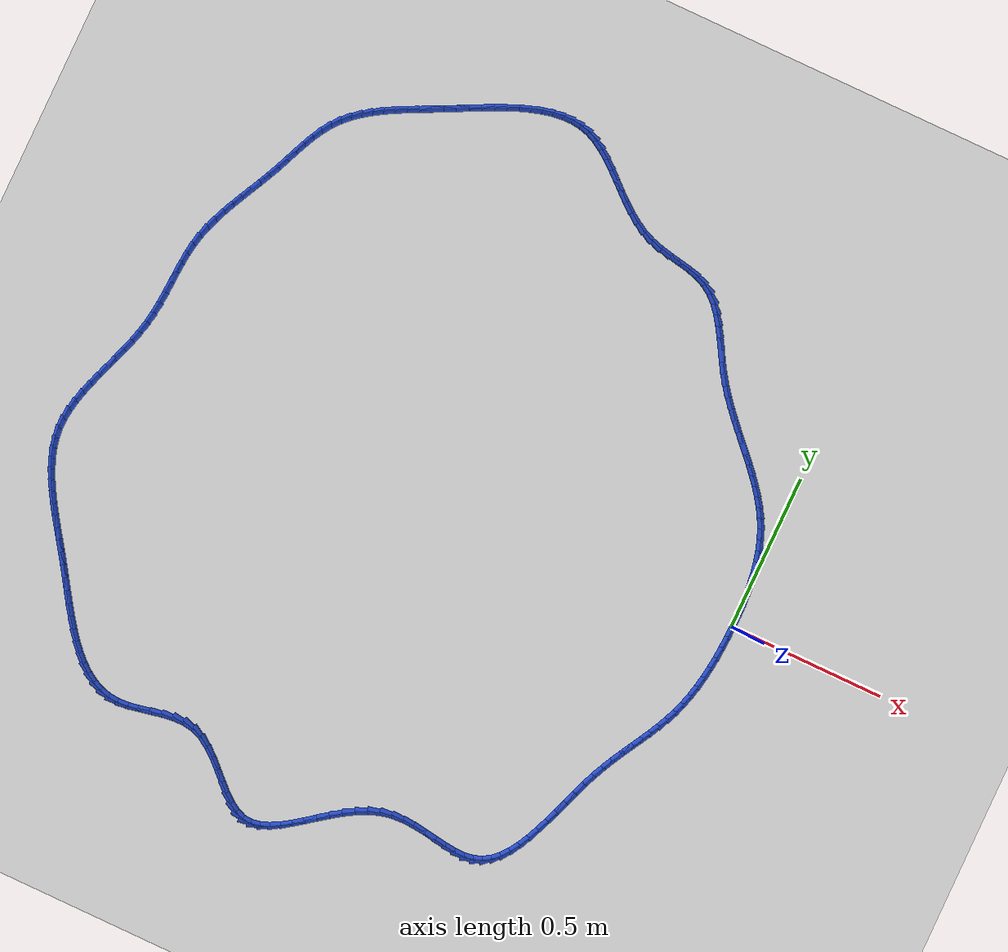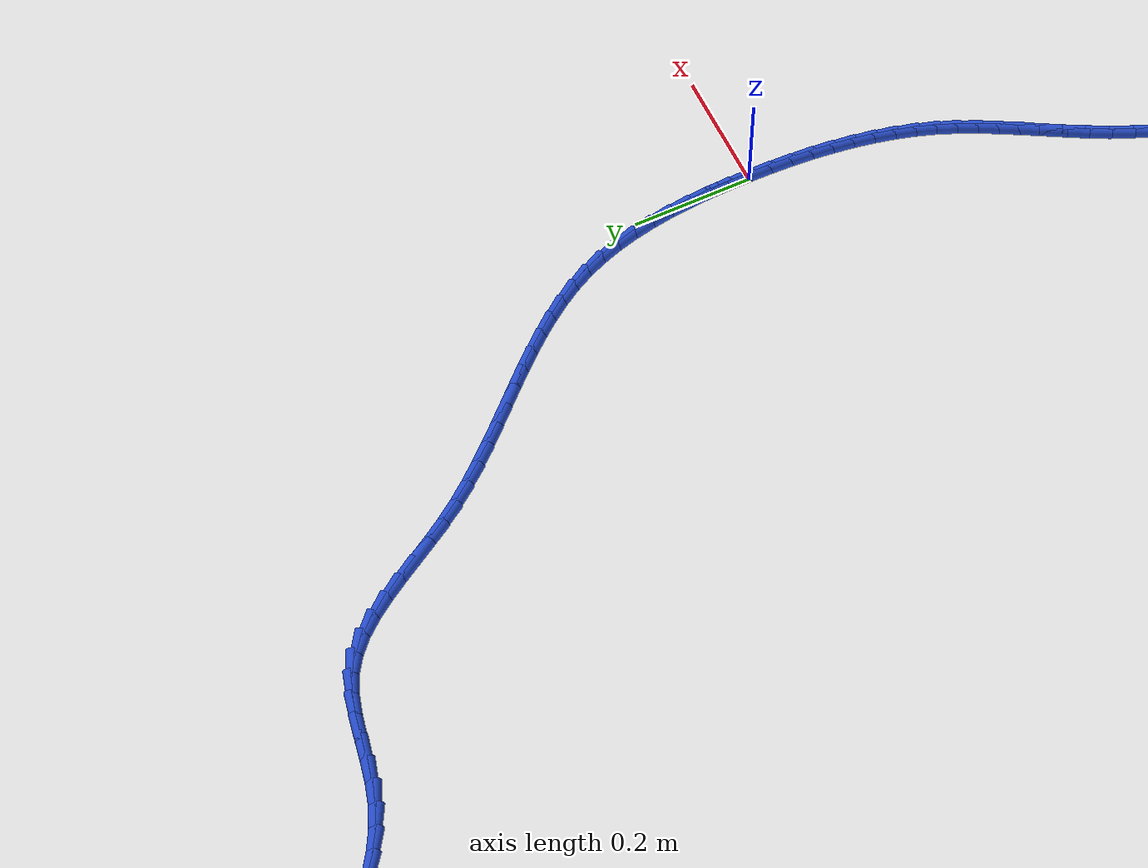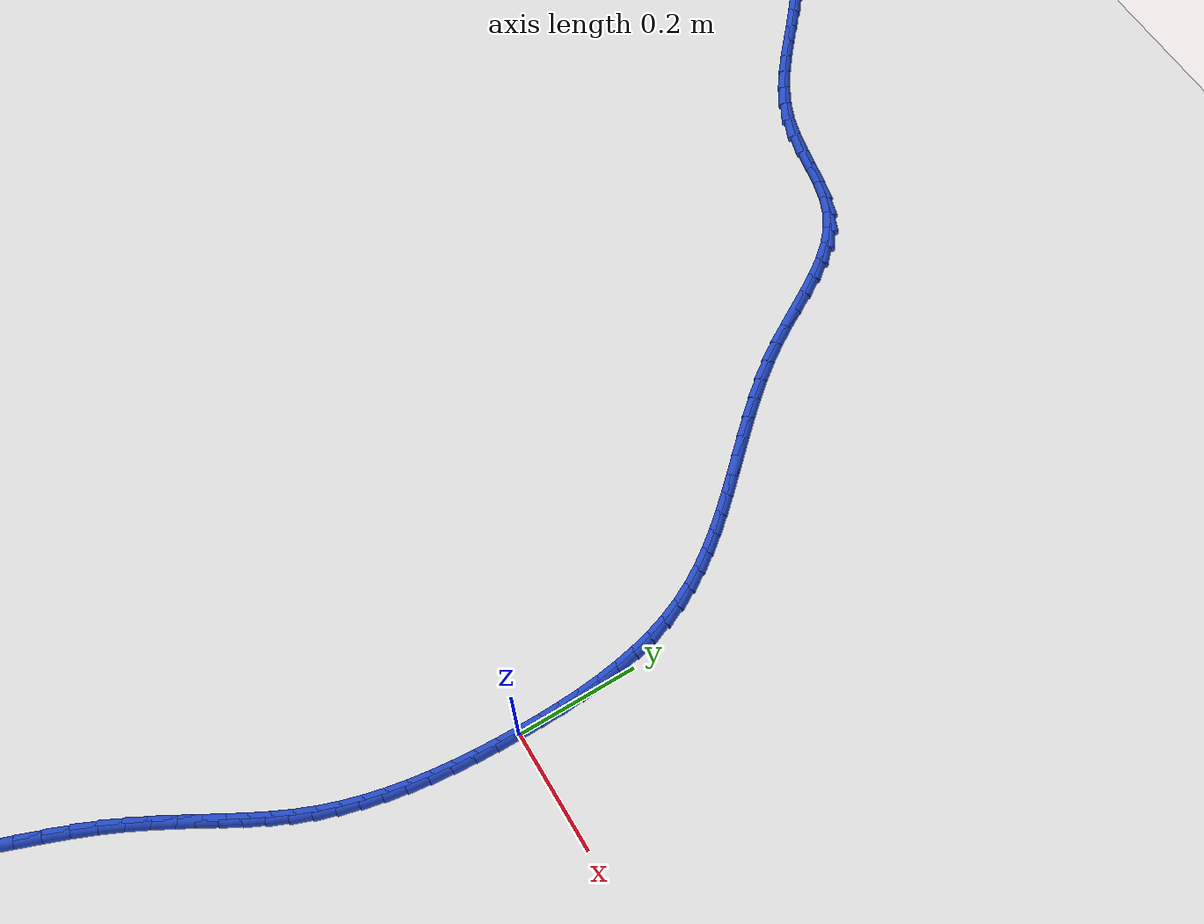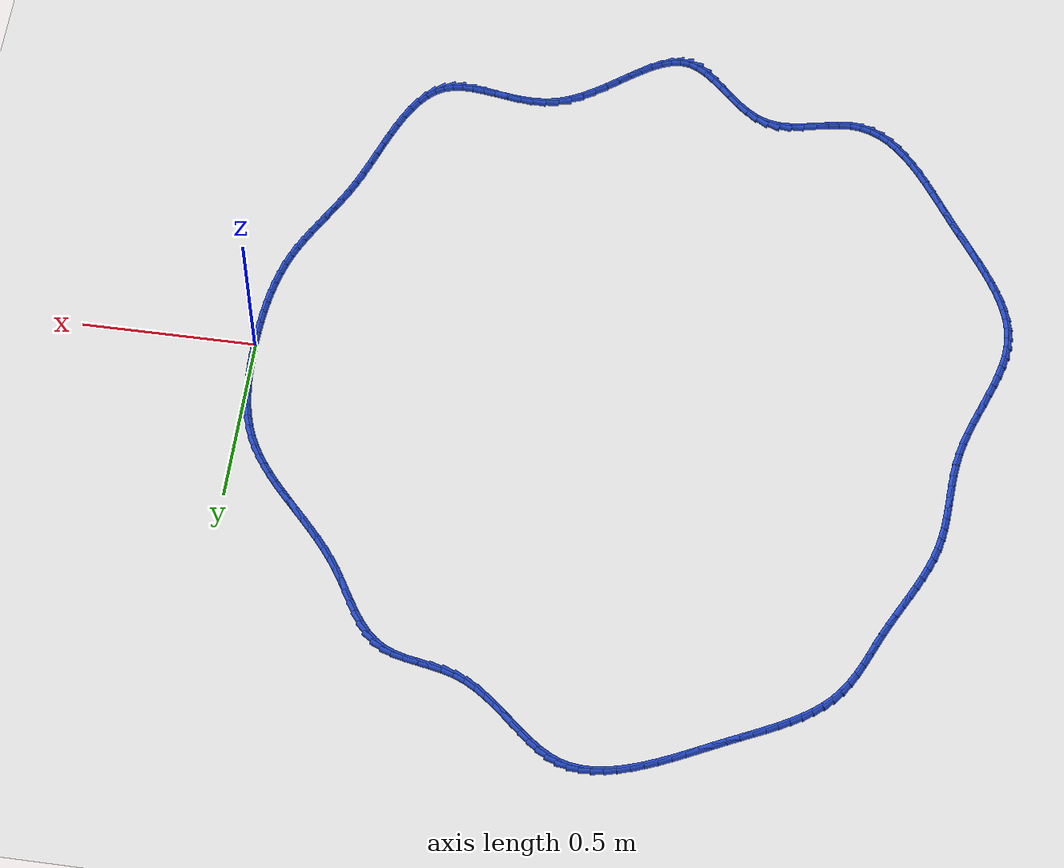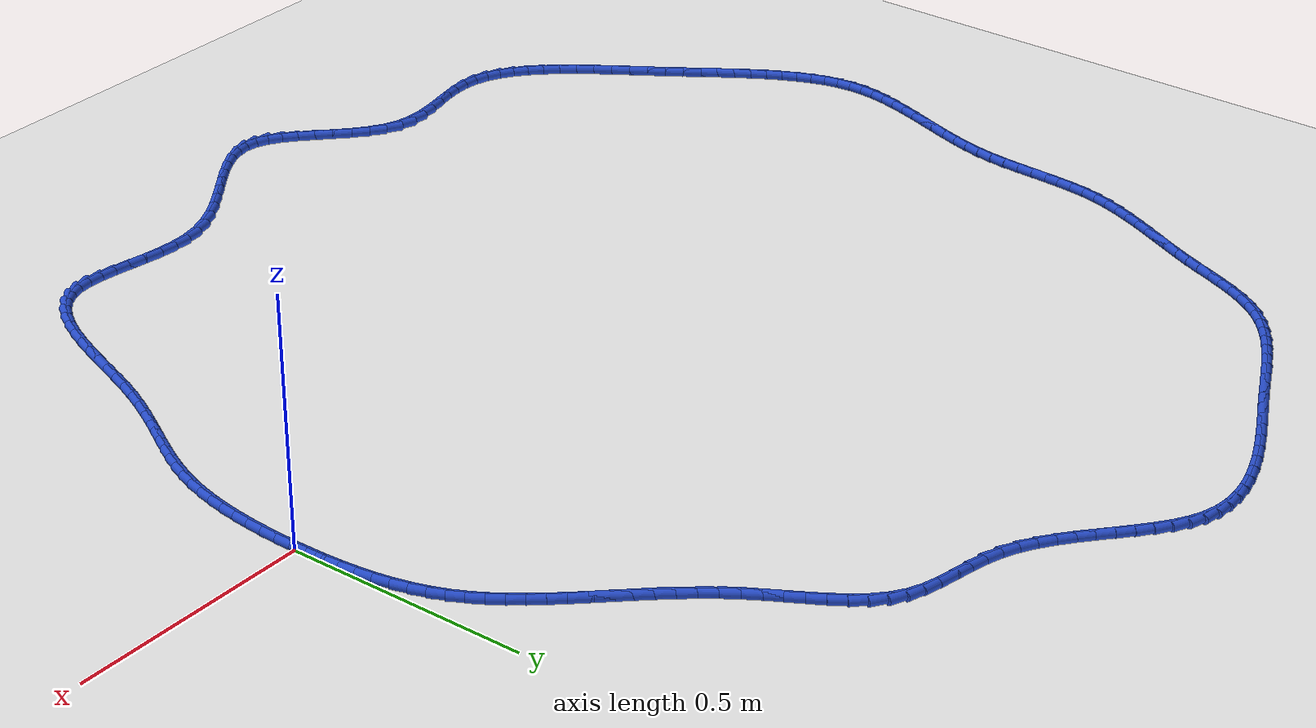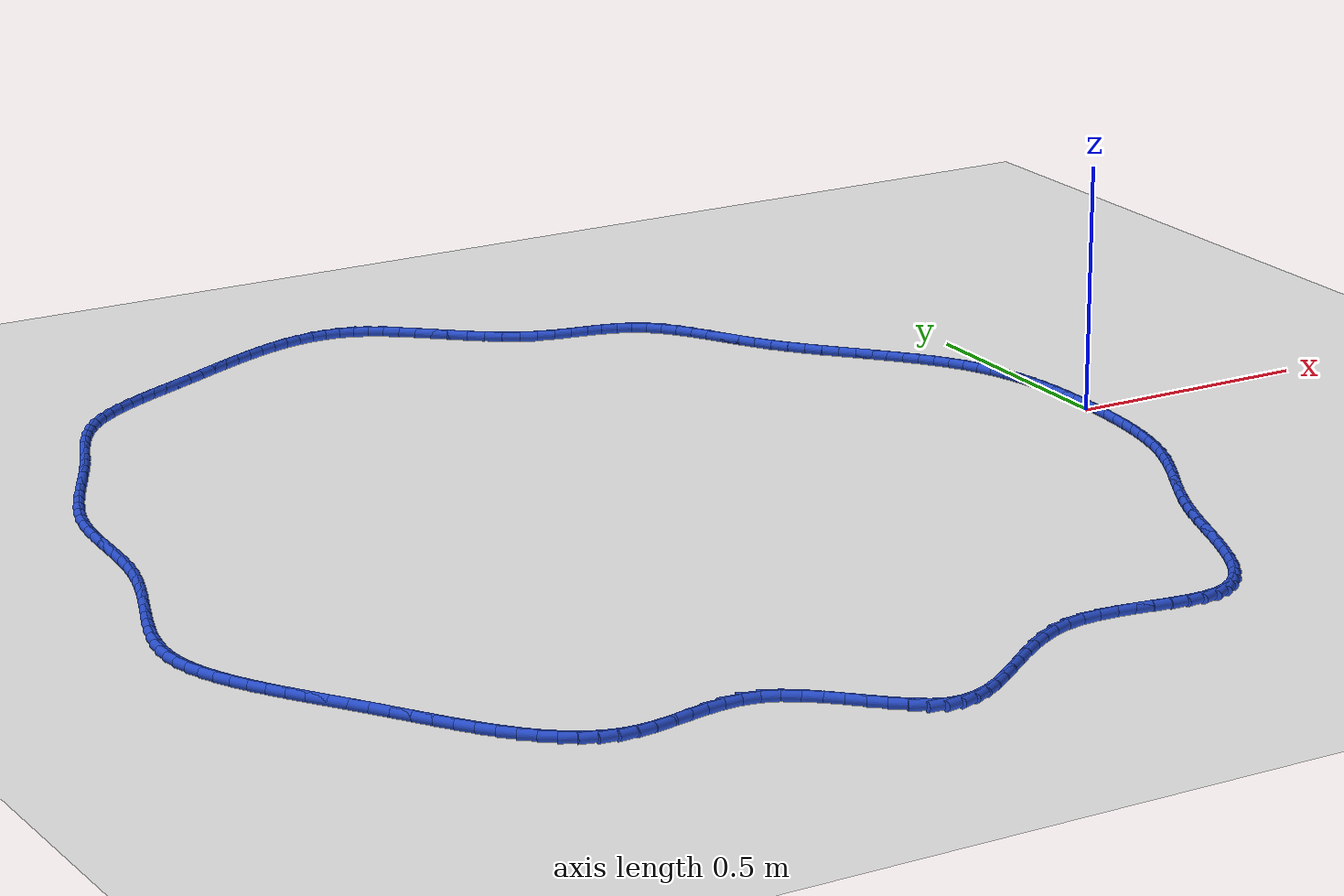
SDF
<sdf version="1.6">
 <world name="default">
  <light name="sun" type="directional">
   <pose>0 0 10 0 -0 0</pose>
   <diffuse>0.8 0.8 0.8 1</diffuse>
   <specular>0.2 0.2 0.2 1</specular>
   <attenuation>
    <range>1000</range>
    <constant>0.9</constant>
    <linear>0.01</linear>
    <quadratic>0.001</quadratic>
   </attenuation>
   <direction>-0.5 0.1 -0.9</direction>
  </light>
  <model name="ground_plane">
   <static>1</static>
   <link name="link">
    <collision name="collision">
     <geometry><plane><normal>0 0 1</normal><size>100 100</size></plane></geometry>
     <surface><friction><ode><mu>100</mu><mu2>50</mu2></ode></friction></surface>
    </collision>
    <visual name="visual">
     <cast_shadows>0</cast_shadows>
     <geometry><plane><normal>0 0 1</normal><size>100 100</size></plane></geometry>
     <material>
      <script><uri>file://media/materials/scripts/gazebo.material</uri><name>Gazebo/WhiteGlow</name></script>
     </material>
    </visual>
   </link>
  </model>
  <gravity>0 0 -9.8</gravity>
  <magnetic_field>6e-06 2.3e-05 -4.2e-05</magnetic_field>
  <atmosphere type="adiabatic"/>
  <physics name="default_physics" default="0" type="ode">
   <max_step_size>0.001</max_step_size>
   <real_time_factor>1</real_time_factor>
   <real_time_update_rate>1000</real_time_update_rate>
  </physics>
  <scene><ambient>0.4 0.4 0.4 1</ambient><background>0.7 0.7 0.7 1</background><shadows>1</shadows></scene>
  <spherical_coordinates>
   <surface_model>EARTH_WGS84</surface_model>
   <latitude_deg>0</latitude_deg>
   <longitude_deg>0</longitude_deg>
   <elevation>0</elevation>
   <heading_deg>0</heading_deg>
  </spherical_coordinates>
  <model name="line">
   <link name="link_0">
    <pose>-1.2576745200831851e-17 -1.457167719820518e-16 0.01 0 1.57 1.5697502538254684</pose>
    <collision name="collision">
     <geometry><cylinder><radius>0.01</radius><length>0.08</length></cylinder></geometry>
    </collision>
    <visual name="visual">
     <material>
      <script><name>Gazebo/Blue</name><uri>file://media/materials/scripts/gazebo.material</uri></script>
     </material>
     <geometry><cylinder><radius>0.01</radius><length>0.08</length></cylinder></geometry>
    </visual>
   </link>
   <link name="link_1">
    <pose>3.7914222122537875e-05 0.03624432463236966 0.01 0 1.57 -1.545426358394945</pose>
    <collision name="collision">
     <geometry><cylinder><radius>0.01</radius><length>0.08</length></cylinder></geometry>
    </collision>
    <visual name="visual">
     <material>
      <script><name>Gazebo/Blue</name><uri>file://media/materials/scripts/gazebo.material</uri></script>
     </material>
     <geometry><cylinder><radius>0.01</radius><length>0.08</length></cylinder></geometry>
    </visual>
   </link>
   <link name="link_2">
    <pose>-0.0008799646611043588 0.07241630300828511 0.01 0 1.57 -1.513676365276203</pose>
    <collision name="collision">
     <geometry><cylinder><radius>0.01</radius><length>0.08</length></cylinder></geometry>
    </collision>
    <visual name="visual">
     <material>
      <script><name>Gazebo/Blue</name><uri>file://media/materials/scripts/gazebo.material</uri></script>
     </material>
     <geometry><cylinder><radius>0.01</radius><length>0.08</length></cylinder></geometry>
    </visual>
   </link>
   <link name="link_3">
    <pose>-0.002934808854095043 0.10835135756664083 0.01 0 1.57 -1.476156049259588</pose>
    <collision name="collision">
     <geometry><cylinder><radius>0.01</radius><length>0.08</length></cylinder></geometry>
    </collision>
    <visual name="visual">
     <material>
      <script><name>Gazebo/Blue</name><uri>file://media/materials/scripts/gazebo.material</uri></script>
     </material>
     <geometry><cylinder><radius>0.01</radius><length>0.08</length></cylinder></geometry>
    </visual>
   </link>
   <link name="link_4">
    <pose>-0.006307790561263857 0.1438849107463313 0.01 0 1.57 -1.4323499008135117</pose>
    <collision name="collision">
     <geometry><cylinder><radius>0.01</radius><length>0.08</length></cylinder></geometry>
    </collision>
    <visual name="visual">
     <material>
      <script><name>Gazebo/Blue</name><uri>file://media/materials/scripts/gazebo.material</uri></script>
     </material>
     <geometry><cylinder><radius>0.01</radius><length>0.08</length></cylinder></geometry>
    </visual>
   </link>
   <link name="link_5">
    <pose>-0.011180081987025135 0.17885238498625114 0.01 0 1.57 -1.3816878339021579</pose>
    <collision name="collision">
     <geometry><cylinder><radius>0.01</radius><length>0.08</length></cylinder></geometry>
    </collision>
    <visual name="visual">
     <material>
      <script><name>Gazebo/Blue</name><uri>file://media/materials/scripts/gazebo.material</uri></script>
     </material>
     <geometry><cylinder><radius>0.01</radius><length>0.08</length></cylinder></geometry>
    </visual>
   </link>
   <link name="link_6">
    <pose>-0.017732855335793215 0.21308920272529502 0.01 0 1.57 -1.3235879838514422</pose>
    <collision name="collision">
     <geometry><cylinder><radius>0.01</radius><length>0.08</length></cylinder></geometry>
    </collision>
    <visual name="visual">
     <material>
      <script><name>Gazebo/Blue</name><uri>file://media/materials/scripts/gazebo.material</uri></script>
     </material>
     <geometry><cylinder><radius>0.01</radius><length>0.08</length></cylinder></geometry>
    </visual>
   </link>
   <link name="link_7">
    <pose>-0.026147282811982454 0.24643078640235747 0.01 0 1.57 -1.257526359712742</pose>
    <collision name="collision">
     <geometry><cylinder><radius>0.01</radius><length>0.08</length></cylinder></geometry>
    </collision>
    <visual name="visual">
     <material>
      <script><name>Gazebo/Blue</name><uri>file://media/materials/scripts/gazebo.material</uri></script>
     </material>
     <geometry><cylinder><radius>0.01</radius><length>0.08</length></cylinder></geometry>
    </visual>
   </link>
   <link name="link_8">
    <pose>-0.03660453662000715 0.27871255845633297 0.01 0 1.57 -1.1831409296070645</pose>
    <collision name="collision">
     <geometry><cylinder><radius>0.01</radius><length>0.08</length></cylinder></geometry>
    </collision>
    <visual name="visual">
     <material>
      <script><name>Gazebo/Blue</name><uri>file://media/materials/scripts/gazebo.material</uri></script>
     </material>
     <geometry><cylinder><radius>0.01</radius><length>0.08</length></cylinder></geometry>
    </visual>
   </link>
   <link name="link_9">
    <pose>-0.049285787808515905 0.30976994225653803 0.01 0 1.57 -1.1034608789886708</pose>
    <collision name="collision">
     <geometry><cylinder><radius>0.01</radius><length>0.08</length></cylinder></geometry>
    </collision>
    <visual name="visual">
     <material>
      <script><name>Gazebo/Blue</name><uri>file://media/materials/scripts/gazebo.material</uri></script>
     </material>
     <geometry><cylinder><radius>0.01</radius><length>0.08</length></cylinder></geometry>
    </visual>
   </link>
   <link name="link_10">
    <pose>-0.06429029239537064 0.3395043049179422 0.01 0 1.57 -1.030679955492988</pose>
    <collision name="collision">
     <geometry><cylinder><radius>0.01</radius><length>0.08</length></cylinder></geometry>
    </collision>
    <visual name="visual">
     <material>
      <script><name>Gazebo/Blue</name><uri>file://media/materials/scripts/gazebo.material</uri></script>
     </material>
     <geometry><cylinder><radius>0.01</radius><length>0.08</length></cylinder></geometry>
    </visual>
   </link>
   <link name="link_11">
    <pose>-0.0814130886452059 0.36806191681624084 0.01 0 1.57 -0.9684711311641314</pose>
    <collision name="collision">
     <geometry><cylinder><radius>0.01</radius><length>0.08</length></cylinder></geometry>
    </collision>
    <visual name="visual">
     <material>
      <script><name>Gazebo/Blue</name><uri>file://media/materials/scripts/gazebo.material</uri></script>
     </material>
     <geometry><cylinder><radius>0.01</radius><length>0.08</length></cylinder></geometry>
    </visual>
   </link>
   <link name="link_12">
    <pose>-0.10037860725663243 0.3956458892674348 0.01 0 1.57 -0.9172846801272387</pose>
    <collision name="collision">
     <geometry><cylinder><radius>0.01</radius><length>0.08</length></cylinder></geometry>
    </collision>
    <visual name="visual">
     <material>
      <script><name>Gazebo/Blue</name><uri>file://media/materials/scripts/gazebo.material</uri></script>
     </material>
     <geometry><cylinder><radius>0.01</radius><length>0.08</length></cylinder></geometry>
    </visual>
   </link>
   <link name="link_13">
    <pose>-0.12091127892826103 0.4224593335875253 0.01 0 1.57 -0.8771255958523567</pose>
    <collision name="collision">
     <geometry><cylinder><radius>0.01</radius><length>0.08</length></cylinder></geometry>
    </collision>
    <visual name="visual">
     <material>
      <script><name>Gazebo/Blue</name><uri>file://media/materials/scripts/gazebo.material</uri></script>
     </material>
     <geometry><cylinder><radius>0.01</radius><length>0.08</length></cylinder></geometry>
    </visual>
   </link>
   <link name="link_14">
    <pose>-0.14273553435870243 0.4487053610925131 0.01 0 1.57 -0.8477418922451007</pose>
    <collision name="collision">
     <geometry><cylinder><radius>0.01</radius><length>0.08</length></cylinder></geometry>
    </collision>
    <visual name="visual">
     <material>
      <script><name>Gazebo/Blue</name><uri>file://media/materials/scripts/gazebo.material</uri></script>
     </material>
     <geometry><cylinder><radius>0.01</radius><length>0.08</length></cylinder></geometry>
    </visual>
   </link>
   <link name="link_15">
    <pose>-0.1655758042465673 0.47458708309839903 0.01 0 1.57 -0.8287737561467782</pose>
    <collision name="collision">
     <geometry><cylinder><radius>0.01</radius><length>0.08</length></cylinder></geometry>
    </collision>
    <visual name="visual">
     <material>
      <script><name>Gazebo/Blue</name><uri>file://media/materials/scripts/gazebo.material</uri></script>
     </material>
     <geometry><cylinder><radius>0.01</radius><length>0.08</length></cylinder></geometry>
    </visual>
   </link>
   <link name="link_16">
    <pose>-0.18915651929046648 0.5003076109211843 0.01 0 1.57 -0.8198539406072032</pose>
    <collision name="collision">
     <geometry><cylinder><radius>0.01</radius><length>0.08</length></cylinder></geometry>
    </collision>
    <visual name="visual">
     <material>
      <script><name>Gazebo/Blue</name><uri>file://media/materials/scripts/gazebo.material</uri></script>
     </material>
     <geometry><cylinder><radius>0.01</radius><length>0.08</length></cylinder></geometry>
    </visual>
   </link>
   <link name="link_17">
    <pose>-0.21320211018901075 0.5260700558768696 0.01 0 1.57 -0.8206640360367449</pose>
    <collision name="collision">
     <geometry><cylinder><radius>0.01</radius><length>0.08</length></cylinder></geometry>
    </collision>
    <visual name="visual">
     <material>
      <script><name>Gazebo/Blue</name><uri>file://media/materials/scripts/gazebo.material</uri></script>
     </material>
     <geometry><cylinder><radius>0.01</radius><length>0.08</length></cylinder></geometry>
    </visual>
   </link>
   <link name="link_18">
    <pose>-0.2374370076408108 0.5520775292814563 0.01 0 1.57 -0.8309552527117083</pose>
    <collision name="collision">
     <geometry><cylinder><radius>0.01</radius><length>0.08</length></cylinder></geometry>
    </collision>
    <visual name="visual">
     <material>
      <script><name>Gazebo/Blue</name><uri>file://media/materials/scripts/gazebo.material</uri></script>
     </material>
     <geometry><cylinder><radius>0.01</radius><length>0.08</length></cylinder></geometry>
    </visual>
   </link>
   <link name="link_19">
    <pose>-0.26158564234447745 0.578533142450945 0.01 0 1.57 -0.8505411197937323</pose>
    <collision name="collision">
     <geometry><cylinder><radius>0.01</radius><length>0.08</length></cylinder></geometry>
    </collision>
    <visual name="visual">
     <material>
      <script><name>Gazebo/Blue</name><uri>file://media/materials/scripts/gazebo.material</uri></script>
     </material>
     <geometry><cylinder><radius>0.01</radius><length>0.08</length></cylinder></geometry>
    </visual>
   </link>
   <link name="link_20">
    <pose>-0.28537244499862136 0.6056400067013369 0.01 0 1.57 -0.8792667849789805</pose>
    <collision name="collision">
     <geometry><cylinder><radius>0.01</radius><length>0.08</length></cylinder></geometry>
    </collision>
    <visual name="visual">
     <material>
      <script><name>Gazebo/Blue</name><uri>file://media/materials/scripts/gazebo.material</uri></script>
     </material>
     <geometry><cylinder><radius>0.01</radius><length>0.08</length></cylinder></geometry>
    </visual>
   </link>
   <link name="link_21">
    <pose>-0.30852184630185336 0.6336012333486327 0.01 0 1.57 -0.9169575886428631</pose>
    <collision name="collision">
     <geometry><cylinder><radius>0.01</radius><length>0.08</length></cylinder></geometry>
    </collision>
    <visual name="visual">
     <material>
      <script><name>Gazebo/Blue</name><uri>file://media/materials/scripts/gazebo.material</uri></script>
     </material>
     <geometry><cylinder><radius>0.01</radius><length>0.08</length></cylinder></geometry>
    </visual>
   </link>
   <link name="link_22">
    <pose>-0.33075827695278404 0.6626199337088332 0.01 0 1.57 -0.9633492876350978</pose>
    <collision name="collision">
     <geometry><cylinder><radius>0.01</radius><length>0.08</length></cylinder></geometry>
    </collision>
    <visual name="visual">
     <material>
      <script><name>Gazebo/Blue</name><uri>file://media/materials/scripts/gazebo.material</uri></script>
     </material>
     <geometry><cylinder><radius>0.01</radius><length>0.08</length></cylinder></geometry>
    </visual>
   </link>
   <link name="link_23">
    <pose>-0.3518061758280994 0.6928992094604121 0.01 0 1.57 -1.011482517989629</pose>
    <collision name="collision">
     <geometry><cylinder><radius>0.01</radius><length>0.08</length></cylinder></geometry>
    </collision>
    <visual name="visual">
     <material>
      <script><name>Gazebo/Blue</name><uri>file://media/materials/scripts/gazebo.material</uri></script>
     </material>
     <geometry><cylinder><radius>0.01</radius><length>0.08</length></cylinder></geometry>
    </visual>
   </link>
   <link name="link_24">
    <pose>-0.37155519547360316 0.7244474647039084 0.01 0 1.57 -1.0384056332821554</pose>
    <collision name="collision">
     <geometry><cylinder><radius>0.01</radius><length>0.08</length></cylinder></geometry>
    </collision>
    <visual name="visual">
     <material>
      <script><name>Gazebo/Blue</name><uri>file://media/materials/scripts/gazebo.material</uri></script>
     </material>
     <geometry><cylinder><radius>0.01</radius><length>0.08</length></cylinder></geometry>
    </visual>
   </link>
   <link name="link_25">
    <pose>-0.3904845477219 0.7565783319401469 0.01 0 1.57 -1.0397252882237475</pose>
    <collision name="collision">
     <geometry><cylinder><radius>0.01</radius><length>0.08</length></cylinder></geometry>
    </collision>
    <visual name="visual">
     <material>
      <script><name>Gazebo/Blue</name><uri>file://media/materials/scripts/gazebo.material</uri></script>
     </material>
     <geometry><cylinder><radius>0.01</radius><length>0.08</length></cylinder></geometry>
    </visual>
   </link>
   <link name="link_26">
    <pose>-0.4092048965185392 0.7884505327104591 0.01 0 1.57 -1.0147869288378168</pose>
    <collision name="collision">
     <geometry><cylinder><radius>0.01</radius><length>0.08</length></cylinder></geometry>
    </collision>
    <visual name="visual">
     <material>
      <script><name>Gazebo/Blue</name><uri>file://media/materials/scripts/gazebo.material</uri></script>
     </material>
     <geometry><cylinder><radius>0.01</radius><length>0.08</length></cylinder></geometry>
    </visual>
   </link>
   <link name="link_27">
    <pose>-0.4283269058090702 0.8192227885561769 0.01 0 1.57 -0.9611743554528464</pose>
    <collision name="collision">
     <geometry><cylinder><radius>0.01</radius><length>0.08</length></cylinder></geometry>
    </collision>
    <visual name="visual">
     <material>
      <script><name>Gazebo/Blue</name><uri>file://media/materials/scripts/gazebo.material</uri></script>
     </material>
     <geometry><cylinder><radius>0.01</radius><length>0.08</length></cylinder></geometry>
    </visual>
   </link>
   <link name="link_28">
    <pose>-0.4484612395390418 0.8480538210186314 0.01 0 1.57 -0.8749214806405832</pose>
    <collision name="collision">
     <geometry><cylinder><radius>0.01</radius><length>0.08</length></cylinder></geometry>
    </collision>
    <visual name="visual">
     <material>
      <script><name>Gazebo/Blue</name><uri>file://media/materials/scripts/gazebo.material</uri></script>
     </material>
     <geometry><cylinder><radius>0.01</radius><length>0.08</length></cylinder></geometry>
    </visual>
   </link>
   <link name="link_29">
    <pose>-0.4702185616540038 0.874102351639154 0.01 0 1.57 -0.7516675667884567</pose>
    <collision name="collision">
     <geometry><cylinder><radius>0.01</radius><length>0.08</length></cylinder></geometry>
    </collision>
    <visual name="visual">
     <material>
      <script><name>Gazebo/Blue</name><uri>file://media/materials/scripts/gazebo.material</uri></script>
     </material>
     <geometry><cylinder><radius>0.01</radius><length>0.08</length></cylinder></geometry>
    </visual>
   </link>
   <link name="link_30">
    <pose>-0.49420953609950513 0.8965271019590766 0.01 0 1.57 -0.5897933921131159</pose>
    <collision name="collision">
     <geometry><cylinder><radius>0.01</radius><length>0.08</length></cylinder></geometry>
    </collision>
    <visual name="visual">
     <material>
      <script><name>Gazebo/Blue</name><uri>file://media/materials/scripts/gazebo.material</uri></script>
     </material>
     <geometry><cylinder><radius>0.01</radius><length>0.08</length></cylinder></geometry>
    </visual>
   </link>
   <link name="link_31">
    <pose>-0.5210448268210953 0.9144867935197305 0.01 0 1.57 -0.4097288504628345</pose>
    <collision name="collision">
     <geometry><cylinder><radius>0.01</radius><length>0.08</length></cylinder></geometry>
    </collision>
    <visual name="visual">
     <material>
      <script><name>Gazebo/Blue</name><uri>file://media/materials/scripts/gazebo.material</uri></script>
     </material>
     <geometry><cylinder><radius>0.01</radius><length>0.08</length></cylinder></geometry>
    </visual>
   </link>
   <link name="link_32">
    <pose>-0.5510934116767741 0.9275371605055613 0.01 0 1.57 -0.2778928901029603</pose>
    <collision name="collision">
     <geometry><cylinder><radius>0.01</radius><length>0.08</length></cylinder></geometry>
    </collision>
    <visual name="visual">
     <material>
      <script><name>Gazebo/Blue</name><uri>file://media/materials/scripts/gazebo.material</uri></script>
     </material>
     <geometry><cylinder><radius>0.01</radius><length>0.08</length></cylinder></geometry>
    </visual>
   </link>
   <link name="link_33">
    <pose>-0.5837401966307707 0.9368504512641631 0.01 0 1.57 -0.20532419274965513</pose>
    <collision name="collision">
     <geometry><cylinder><radius>0.01</radius><length>0.08</length></cylinder></geometry>
    </collision>
    <visual name="visual">
     <material>
      <script><name>Gazebo/Blue</name><uri>file://media/materials/scripts/gazebo.material</uri></script>
     </material>
     <geometry><cylinder><radius>0.01</radius><length>0.08</length></cylinder></geometry>
    </visual>
   </link>
   <link name="link_34">
    <pose>-0.6181196604270734 0.9440102856607198 0.01 0 1.57 -0.18483417914882785</pose>
    <collision name="collision">
     <geometry><cylinder><radius>0.01</radius><length>0.08</length></cylinder></geometry>
    </collision>
    <visual name="visual">
     <material>
      <script><name>Gazebo/Blue</name><uri>file://media/materials/scripts/gazebo.material</uri></script>
     </material>
     <geometry><cylinder><radius>0.01</radius><length>0.08</length></cylinder></geometry>
    </visual>
   </link>
   <link name="link_35">
    <pose>-0.6533662817585869 0.9506002836443302 0.01 0 1.57 -0.21246498933983246</pose>
    <collision name="collision">
     <geometry><cylinder><radius>0.01</radius><length>0.08</length></cylinder></geometry>
    </collision>
    <visual name="visual">
     <material>
      <script><name>Gazebo/Blue</name><uri>file://media/materials/scripts/gazebo.material</uri></script>
     </material>
     <geometry><cylinder><radius>0.01</radius><length>0.08</length></cylinder></geometry>
    </visual>
   </link>
   <link name="link_36">
    <pose>-0.6886145393182147 0.9582040651640937 0.01 0 1.57 -0.28840893188313016</pose>
    <collision name="collision">
     <geometry><cylinder><radius>0.01</radius><length>0.08</length></cylinder></geometry>
    </collision>
    <visual name="visual">
     <material>
      <script><name>Gazebo/Blue</name><uri>file://media/materials/scripts/gazebo.material</uri></script>
     </material>
     <geometry><cylinder><radius>0.01</radius><length>0.08</length></cylinder></geometry>
    </visual>
   </link>
   <link name="link_37">
    <pose>-0.7229989117988616 0.9684052501691085 0.01 0 1.57 -0.4070965581341074</pose>
    <collision name="collision">
     <geometry><cylinder><radius>0.01</radius><length>0.08</length></cylinder></geometry>
    </collision>
    <visual name="visual">
     <material>
      <script><name>Gazebo/Blue</name><uri>file://media/materials/scripts/gazebo.material</uri></script>
     </material>
     <geometry><cylinder><radius>0.01</radius><length>0.08</length></cylinder></geometry>
    </visual>
   </link>
   <link name="link_38">
    <pose>-0.7557713475280352 0.9825361880043053 0.01 0 1.57 -0.5196916320810838</pose>
    <collision name="collision">
     <geometry><cylinder><radius>0.01</radius><length>0.08</length></cylinder></geometry>
    </collision>
    <visual name="visual">
     <material>
      <script><name>Gazebo/Blue</name><uri>file://media/materials/scripts/gazebo.material</uri></script>
     </material>
     <geometry><cylinder><radius>0.01</radius><length>0.08</length></cylinder></geometry>
    </visual>
   </link>
   <link name="link_39">
    <pose>-0.7869187091929236 1.00035722708185 0.01 0 1.57 -0.6064296843038713</pose>
    <collision name="collision">
     <geometry><cylinder><radius>0.01</radius><length>0.08</length></cylinder></geometry>
    </collision>
    <visual name="visual">
     <material>
      <script><name>Gazebo/Blue</name><uri>file://media/materials/scripts/gazebo.material</uri></script>
     </material>
     <geometry><cylinder><radius>0.01</radius><length>0.08</length></cylinder></geometry>
    </visual>
   </link>
   <link name="link_40">
    <pose>-0.8167114884633406 1.0210220260419964 0.01 0 1.57 -0.6681969730887816</pose>
    <collision name="collision">
     <geometry><cylinder><radius>0.01</radius><length>0.08</length></cylinder></geometry>
    </collision>
    <visual name="visual">
     <material>
      <script><name>Gazebo/Blue</name><uri>file://media/materials/scripts/gazebo.material</uri></script>
     </material>
     <geometry><cylinder><radius>0.01</radius><length>0.08</length></cylinder></geometry>
    </visual>
   </link>
   <link name="link_41">
    <pose>-0.845420781855653 1.0436829497424895 0.01 0 1.57 -0.7065101633793706</pose>
    <collision name="collision">
     <geometry><cylinder><radius>0.01</radius><length>0.08</length></cylinder></geometry>
    </collision>
    <visual name="visual">
     <material>
      <script><name>Gazebo/Blue</name><uri>file://media/materials/scripts/gazebo.material</uri></script>
     </material>
     <geometry><cylinder><radius>0.01</radius><length>0.08</length></cylinder></geometry>
    </visual>
   </link>
   <link name="link_42">
    <pose>-0.8733176858862273 1.067492363041074 0.01 0 1.57 -0.7224233884377397</pose>
    <collision name="collision">
     <geometry><cylinder><radius>0.01</radius><length>0.08</length></cylinder></geometry>
    </collision>
    <visual name="visual">
     <material>
      <script><name>Gazebo/Blue</name><uri>file://media/materials/scripts/gazebo.material</uri></script>
     </material>
     <geometry><cylinder><radius>0.01</radius><length>0.08</length></cylinder></geometry>
    </visual>
   </link>
   <link name="link_43">
    <pose>-0.9006732970714307 1.0916026307954945 0.01 0 1.57 -0.7159738012784749</pose>
    <collision name="collision">
     <geometry><cylinder><radius>0.01</radius><length>0.08</length></cylinder></geometry>
    </collision>
    <visual name="visual">
     <material>
      <script><name>Gazebo/Blue</name><uri>file://media/materials/scripts/gazebo.material</uri></script>
     </material>
     <geometry><cylinder><radius>0.01</radius><length>0.08</length></cylinder></geometry>
    </visual>
   </link>
   <link name="link_44">
    <pose>-0.9277587119276302 1.115166117863495 0.01 0 1.57 -0.685896250720218</pose>
    <collision name="collision">
     <geometry><cylinder><radius>0.01</radius><length>0.08</length></cylinder></geometry>
    </collision>
    <visual name="visual">
     <material>
      <script><name>Gazebo/Blue</name><uri>file://media/materials/scripts/gazebo.material</uri></script>
     </material>
     <geometry><cylinder><radius>0.01</radius><length>0.08</length></cylinder></geometry>
    </visual>
   </link>
   <link name="link_45">
    <pose>-0.9548450269711918 1.1373351891028205 0.01 0 1.57 -0.6295147038442278</pose>
    <collision name="collision">
     <geometry><cylinder><radius>0.01</radius><length>0.08</length></cylinder></geometry>
    </collision>
    <visual name="visual">
     <material>
      <script><name>Gazebo/Blue</name><uri>file://media/materials/scripts/gazebo.material</uri></script>
     </material>
     <geometry><cylinder><radius>0.01</radius><length>0.08</length></cylinder></geometry>
    </visual>
   </link>
   <link name="link_46">
    <pose>-0.982203338718483 1.1572622093712155 0.01 0 1.57 -0.5429584819927106</pose>
    <collision name="collision">
     <geometry><cylinder><radius>0.01</radius><length>0.08</length></cylinder></geometry>
    </collision>
    <visual name="visual">
     <material>
      <script><name>Gazebo/Blue</name><uri>file://media/materials/scripts/gazebo.material</uri></script>
     </material>
     <geometry><cylinder><radius>0.01</radius><length>0.08</length></cylinder></geometry>
    </visual>
   </link>
   <link name="link_47">
    <pose>-1.0101047436858706 1.1740995435264248 0.01 0 1.57 -0.42221648896035374</pose>
    <collision name="collision">
     <geometry><cylinder><radius>0.01</radius><length>0.08</length></cylinder></geometry>
    </collision>
    <visual name="visual">
     <material>
      <script><name>Gazebo/Blue</name><uri>file://media/materials/scripts/gazebo.material</uri></script>
     </material>
     <geometry><cylinder><radius>0.01</radius><length>0.08</length></cylinder></geometry>
    </visual>
   </link>
   <link name="link_48">
    <pose>-1.0388203383897205 1.1869995564261926 0.01 0 1.57 -0.2704729338988285</pose>
    <collision name="collision">
     <geometry><cylinder><radius>0.01</radius><length>0.08</length></cylinder></geometry>
    </collision>
    <visual name="visual">
     <material>
      <script><name>Gazebo/Blue</name><uri>file://media/materials/scripts/gazebo.material</uri></script>
     </material>
     <geometry><cylinder><radius>0.01</radius><length>0.08</length></cylinder></geometry>
    </visual>
   </link>
   <link name="link_49">
    <pose>-1.0685804066658937 1.1952510520163342 0.01 0 1.57 -0.12034381612702377</pose>
    <collision name="collision">
     <geometry><cylinder><radius>0.01</radius><length>0.08</length></cylinder></geometry>
    </collision>
    <visual name="visual">
     <material>
      <script><name>Gazebo/Blue</name><uri>file://media/materials/scripts/gazebo.material</uri></script>
     </material>
     <geometry><cylinder><radius>0.01</radius><length>0.08</length></cylinder></geometry>
    </visual>
   </link>
   <link name="link_50">
    <pose>-1.0993666162380464 1.1989739718990957 0.01 0 1.57 0.011758414931012992</pose>
    <collision name="collision">
     <geometry><cylinder><radius>0.01</radius><length>0.08</length></cylinder></geometry>
    </collision>
    <visual name="visual">
     <material>
      <script><name>Gazebo/Blue</name><uri>file://media/materials/scripts/gazebo.material</uri></script>
     </material>
     <geometry><cylinder><radius>0.01</radius><length>0.08</length></cylinder></geometry>
    </visual>
   </link>
   <link name="link_51">
    <pose>-1.1310670227326935 1.1986012081864146 0.01 0 1.57 0.12351198069109004</pose>
    <collision name="collision">
     <geometry><cylinder><radius>0.01</radius><length>0.08</length></cylinder></geometry>
    </collision>
    <visual name="visual">
     <material>
      <script><name>Gazebo/Blue</name><uri>file://media/materials/scripts/gazebo.material</uri></script>
     </material>
     <geometry><cylinder><radius>0.01</radius><length>0.08</length></cylinder></geometry>
    </visual>
   </link>
   <link name="link_52">
    <pose>-1.163569511467243 1.1945662223431561 0.01 0 1.57 0.21544098257447505</pose>
    <collision name="collision">
     <geometry><cylinder><radius>0.01</radius><length>0.08</length></cylinder></geometry>
    </collision>
    <visual name="visual">
     <material>
      <script><name>Gazebo/Blue</name><uri>file://media/materials/scripts/gazebo.material</uri></script>
     </material>
     <geometry><cylinder><radius>0.01</radius><length>0.08</length></cylinder></geometry>
    </visual>
   </link>
   <link name="link_53">
    <pose>-1.196761967759104 1.187302475834186 0.01 0 1.57 0.2894983595741678</pose>
    <collision name="collision">
     <geometry><cylinder><radius>0.01</radius><length>0.08</length></cylinder></geometry>
    </collision>
    <visual name="visual">
     <material>
      <script><name>Gazebo/Blue</name><uri>file://media/materials/scripts/gazebo.material</uri></script>
     </material>
     <geometry><cylinder><radius>0.01</radius><length>0.08</length></cylinder></geometry>
    </visual>
   </link>
   <link name="link_54">
    <pose>-1.2305322769256848 1.1772434301243684 0.01 0 1.57 0.3480332926107759</pose>
    <collision name="collision">
     <geometry><cylinder><radius>0.01</radius><length>0.08</length></cylinder></geometry>
    </collision>
    <visual name="visual">
     <material>
      <script><name>Gazebo/Blue</name><uri>file://media/materials/scripts/gazebo.material</uri></script>
     </material>
     <geometry><cylinder><radius>0.01</radius><length>0.08</length></cylinder></geometry>
    </visual>
   </link>
   <link name="link_55">
    <pose>-1.2647683242843935 1.1648225466785695 0.01 0 1.57 0.39323565058645565</pose>
    <collision name="collision">
     <geometry><cylinder><radius>0.01</radius><length>0.08</length></cylinder></geometry>
    </collision>
    <visual name="visual">
     <material>
      <script><name>Gazebo/Blue</name><uri>file://media/materials/scripts/gazebo.material</uri></script>
     </material>
     <geometry><cylinder><radius>0.01</radius><length>0.08</length></cylinder></geometry>
    </visual>
   </link>
   <link name="link_56">
    <pose>-1.299357995152639 1.1504732869616547 0.01 0 1.57 0.42690870299146344</pose>
    <collision name="collision">
     <geometry><cylinder><radius>0.01</radius><length>0.08</length></cylinder></geometry>
    </collision>
    <visual name="visual">
     <material>
      <script><name>Gazebo/Blue</name><uri>file://media/materials/scripts/gazebo.material</uri></script>
     </material>
     <geometry><cylinder><radius>0.01</radius><length>0.08</length></cylinder></geometry>
    </visual>
   </link>
   <link name="link_57">
    <pose>-1.3341891748478303 1.1346291124384889 0.01 0 1.57 0.4504114732110434</pose>
    <collision name="collision">
     <geometry><cylinder><radius>0.01</radius><length>0.08</length></cylinder></geometry>
    </collision>
    <visual name="visual">
     <material>
      <script><name>Gazebo/Blue</name><uri>file://media/materials/scripts/gazebo.material</uri></script>
     </material>
     <geometry><cylinder><radius>0.01</radius><length>0.08</length></cylinder></geometry>
    </visual>
   </link>
   <link name="link_58">
    <pose>-1.3691497486873747 1.1177234845739368 0.01 0 1.57 0.4646692896271354</pose>
    <collision name="collision">
     <geometry><cylinder><radius>0.01</radius><length>0.08</length></cylinder></geometry>
    </collision>
    <visual name="visual">
     <material>
      <script><name>Gazebo/Blue</name><uri>file://media/materials/scripts/gazebo.material</uri></script>
     </material>
     <geometry><cylinder><radius>0.01</radius><length>0.08</length></cylinder></geometry>
    </visual>
   </link>
   <link name="link_59">
    <pose>-1.404127601988682 1.1001898648328645 0.01 0 1.57 0.4701997474381013</pose>
    <collision name="collision">
     <geometry><cylinder><radius>0.01</radius><length>0.08</length></cylinder></geometry>
    </collision>
    <visual name="visual">
     <material>
      <script><name>Gazebo/Blue</name><uri>file://media/materials/scripts/gazebo.material</uri></script>
     </material>
     <geometry><cylinder><radius>0.01</radius><length>0.08</length></cylinder></geometry>
    </visual>
   </link>
   <link name="link_60">
    <pose>-1.4390106200691601 1.082461714680137 0.01 0 1.57 0.46712946160996177</pose>
    <collision name="collision">
     <geometry><cylinder><radius>0.01</radius><length>0.08</length></cylinder></geometry>
    </collision>
    <visual name="visual">
     <material>
      <script><name>Gazebo/Blue</name><uri>file://media/materials/scripts/gazebo.material</uri></script>
     </material>
     <geometry><cylinder><radius>0.01</radius><length>0.08</length></cylinder></geometry>
    </visual>
   </link>
   <link name="link_61">
    <pose>-1.473686688246218 1.0649724955806195 0.01 0 1.57 0.4578661687066375</pose>
    <collision name="collision">
     <geometry><cylinder><radius>0.01</radius><length>0.08</length></cylinder></geometry>
    </collision>
    <visual name="visual">
     <material>
      <script><name>Gazebo/Blue</name><uri>file://media/materials/scripts/gazebo.material</uri></script>
     </material>
     <geometry><cylinder><radius>0.01</radius><length>0.08</length></cylinder></geometry>
    </visual>
   </link>
   <link name="link_62">
    <pose>-1.5080267728773236 1.0480499096312894 0.01 0 1.57 0.45509881952222836</pose>
    <collision name="collision">
     <geometry><cylinder><radius>0.01</radius><length>0.08</length></cylinder></geometry>
    </collision>
    <visual name="visual">
     <material>
      <script><name>Gazebo/Blue</name><uri>file://media/materials/scripts/gazebo.material</uri></script>
     </material>
     <geometry><cylinder><radius>0.01</radius><length>0.08</length></cylinder></geometry>
    </visual>
   </link>
   <link name="link_63">
    <pose>-1.5418204156533917 1.0315126783951352 0.01 0 1.57 0.46316137950109987</pose>
    <collision name="collision">
     <geometry><cylinder><radius>0.01</radius><length>0.08</length></cylinder></geometry>
    </collision>
    <visual name="visual">
     <material>
      <script><name>Gazebo/Blue</name><uri>file://media/materials/scripts/gazebo.material</uri></script>
     </material>
     <geometry><cylinder><radius>0.01</radius><length>0.08</length></cylinder></geometry>
    </visual>
   </link>
   <link name="link_64">
    <pose>-1.5748326939917534 1.0150265987802374 0.01 0 1.57 0.48274278074040394</pose>
    <collision name="collision">
     <geometry><cylinder><radius>0.01</radius><length>0.08</length></cylinder></geometry>
    </collision>
    <visual name="visual">
     <material>
      <script><name>Gazebo/Blue</name><uri>file://media/materials/scripts/gazebo.material</uri></script>
     </material>
     <geometry><cylinder><radius>0.01</radius><length>0.08</length></cylinder></geometry>
    </visual>
   </link>
   <link name="link_65">
    <pose>-1.6068286805450016 0.9982574379106108 0.01 0 1.57 0.5146730862857423</pose>
    <collision name="collision">
     <geometry><cylinder><radius>0.01</radius><length>0.08</length></cylinder></geometry>
    </collision>
    <visual name="visual">
     <material>
      <script><name>Gazebo/Blue</name><uri>file://media/materials/scripts/gazebo.material</uri></script>
     </material>
     <geometry><cylinder><radius>0.01</radius><length>0.08</length></cylinder></geometry>
    </visual>
   </link>
   <link name="link_66">
    <pose>-1.6375734479657313 0.9808709629102708 0.01 0 1.57 0.5598612023097513</pose>
    <collision name="collision">
     <geometry><cylinder><radius>0.01</radius><length>0.08</length></cylinder></geometry>
    </collision>
    <visual name="visual">
     <material>
      <script><name>Gazebo/Blue</name><uri>file://media/materials/scripts/gazebo.material</uri></script>
     </material>
     <geometry><cylinder><radius>0.01</radius><length>0.08</length></cylinder></geometry>
    </visual>
   </link>
   <link name="link_67">
    <pose>-1.6668320689065363 0.9625329409032322 0.01 0 1.57 0.6191455249734222</pose>
    <collision name="collision">
     <geometry><cylinder><radius>0.01</radius><length>0.08</length></cylinder></geometry>
    </collision>
    <visual name="visual">
     <material>
      <script><name>Gazebo/Blue</name><uri>file://media/materials/scripts/gazebo.material</uri></script>
     </material>
     <geometry><cylinder><radius>0.01</radius><length>0.08</length></cylinder></geometry>
    </visual>
   </link>
   <link name="link_68">
    <pose>-1.6943696160200112 0.9429091390135101 0.01 0 1.57 0.6930254264934056</pose>
    <collision name="collision">
     <geometry><cylinder><radius>0.01</radius><length>0.08</length></cylinder></geometry>
    </collision>
    <visual name="visual">
     <material>
      <script><name>Gazebo/Blue</name><uri>file://media/materials/scripts/gazebo.material</uri></script>
     </material>
     <geometry><cylinder><radius>0.01</radius><length>0.08</length></cylinder></geometry>
    </visual>
   </link>
   <link name="link_69">
    <pose>-1.7199511619587493 0.9216653243651196 0.01 0 1.57 0.78126505538493</pose>
    <collision name="collision">
     <geometry><cylinder><radius>0.01</radius><length>0.08</length></cylinder></geometry>
    </collision>
    <visual name="visual">
     <material>
      <script><name>Gazebo/Blue</name><uri>file://media/materials/scripts/gazebo.material</uri></script>
     </material>
     <geometry><cylinder><radius>0.01</radius><length>0.08</length></cylinder></geometry>
    </visual>
   </link>
   <link name="link_70">
    <pose>-1.7433417793753452 0.8984672640820757 0.01 0 1.57 0.8824229732381923</pose>
    <collision name="collision">
     <geometry><cylinder><radius>0.01</radius><length>0.08</length></cylinder></geometry>
    </collision>
    <visual name="visual">
     <material>
      <script><name>Gazebo/Blue</name><uri>file://media/materials/scripts/gazebo.material</uri></script>
     </material>
     <geometry><cylinder><radius>0.01</radius><length>0.08</length></cylinder></geometry>
    </visual>
   </link>
   <link name="link_71">
    <pose>-1.7643068622910218 0.8729810577434927 0.01 0 1.57 0.9854298848311027</pose>
    <collision name="collision">
     <geometry><cylinder><radius>0.01</radius><length>0.08</length></cylinder></geometry>
    </collision>
    <visual name="visual">
     <material>
      <script><name>Gazebo/Blue</name><uri>file://media/materials/scripts/gazebo.material</uri></script>
     </material>
     <geometry><cylinder><radius>0.01</radius><length>0.08</length></cylinder></geometry>
    </visual>
   </link>
   <link name="link_72">
    <pose>-1.7828058153013253 0.845073508416027 0.01 0 1.57 1.0664717966283566</pose>
    <collision name="collision">
     <geometry><cylinder><radius>0.01</radius><length>0.08</length></cylinder></geometry>
    </collision>
    <visual name="visual">
     <material>
      <script><name>Gazebo/Blue</name><uri>file://media/materials/scripts/gazebo.material</uri></script>
     </material>
     <geometry><cylinder><radius>0.01</radius><length>0.08</length></cylinder></geometry>
    </visual>
   </link>
   <link name="link_73">
    <pose>-1.7993204863157415 0.8151518855585327 0.01 0 1.57 1.123047139026396</pose>
    <collision name="collision">
     <geometry><cylinder><radius>0.01</radius><length>0.08</length></cylinder></geometry>
    </collision>
    <visual name="visual">
     <material>
      <script><name>Gazebo/Blue</name><uri>file://media/materials/scripts/gazebo.material</uri></script>
     </material>
     <geometry><cylinder><radius>0.01</radius><length>0.08</length></cylinder></geometry>
    </visual>
   </link>
   <link name="link_74">
    <pose>-1.8144197731592322 0.7837135115647986 0.01 0 1.57 1.1570287606181862</pose>
    <collision name="collision">
     <geometry><cylinder><radius>0.01</radius><length>0.08</length></cylinder></geometry>
    </collision>
    <visual name="visual">
     <material>
      <script><name>Gazebo/Blue</name><uri>file://media/materials/scripts/gazebo.material</uri></script>
     </material>
     <geometry><cylinder><radius>0.01</radius><length>0.08</length></cylinder></geometry>
    </visual>
   </link>
   <link name="link_75">
    <pose>-1.8286725736567584 0.7512557088286127 0.01 0 1.57 1.1699855465790934</pose>
    <collision name="collision">
     <geometry><cylinder><radius>0.01</radius><length>0.08</length></cylinder></geometry>
    </collision>
    <visual name="visual">
     <material>
      <script><name>Gazebo/Blue</name><uri>file://media/materials/scripts/gazebo.material</uri></script>
     </material>
     <geometry><cylinder><radius>0.01</radius><length>0.08</length></cylinder></geometry>
    </visual>
   </link>
   <link name="link_76">
    <pose>-1.8426477856332817 0.7182757997437641 0.01 0 1.57 1.1627947293551688</pose>
    <collision name="collision">
     <geometry><cylinder><radius>0.01</radius><length>0.08</length></cylinder></geometry>
    </collision>
    <visual name="visual">
     <material>
      <script><name>Gazebo/Blue</name><uri>file://media/materials/scripts/gazebo.material</uri></script>
     </material>
     <geometry><cylinder><radius>0.01</radius><length>0.08</length></cylinder></geometry>
    </visual>
   </link>
   <link name="link_77">
    <pose>-1.856914306913763 0.6852711067040409 0.01 0 1.57 1.1388848295778249</pose>
    <collision name="collision">
     <geometry><cylinder><radius>0.01</radius><length>0.08</length></cylinder></geometry>
    </collision>
    <visual name="visual">
     <material>
      <script><name>Gazebo/Blue</name><uri>file://media/materials/scripts/gazebo.material</uri></script>
     </material>
     <geometry><cylinder><radius>0.01</radius><length>0.08</length></cylinder></geometry>
    </visual>
   </link>
   <link name="link_78">
    <pose>-1.87194029643303 0.6526722864763416 0.01 0 1.57 1.1180958443084672</pose>
    <collision name="collision">
     <geometry><cylinder><radius>0.01</radius><length>0.08</length></cylinder></geometry>
    </collision>
    <visual name="visual">
     <material>
      <script><name>Gazebo/Blue</name><uri>file://media/materials/scripts/gazebo.material</uri></script>
     </material>
     <geometry><cylinder><radius>0.01</radius><length>0.08</length></cylinder></geometry>
    </visual>
   </link>
   <link name="link_79">
    <pose>-1.8875851159511101 0.6205071142268895 0.01 0 1.57 1.1079449908210133</pose>
    <collision name="collision">
     <geometry><cylinder><radius>0.01</radius><length>0.08</length></cylinder></geometry>
    </collision>
    <visual name="visual">
     <material>
      <script><name>Gazebo/Blue</name><uri>file://media/materials/scripts/gazebo.material</uri></script>
     </material>
     <geometry><cylinder><radius>0.01</radius><length>0.08</length></cylinder></geometry>
    </visual>
   </link>
   <link name="link_80">
    <pose>-1.9034805865810305 0.588652786334957 0.01 0 1.57 1.1085575019673424</pose>
    <collision name="collision">
     <geometry><cylinder><radius>0.01</radius><length>0.08</length></cylinder></geometry>
    </collision>
    <visual name="visual">
     <material>
      <script><name>Gazebo/Blue</name><uri>file://media/materials/scripts/gazebo.material</uri></script>
     </material>
     <geometry><cylinder><radius>0.01</radius><length>0.08</length></cylinder></geometry>
    </visual>
   </link>
   <link name="link_81">
    <pose>-1.9192581355424398 0.5569862385143558 0.01 0 1.57 1.120138963124015</pose>
    <collision name="collision">
     <geometry><cylinder><radius>0.01</radius><length>0.08</length></cylinder></geometry>
    </collision>
    <visual name="visual">
     <material>
      <script><name>Gazebo/Blue</name><uri>file://media/materials/scripts/gazebo.material</uri></script>
     </material>
     <geometry><cylinder><radius>0.01</radius><length>0.08</length></cylinder></geometry>
    </visual>
   </link>
   <link name="link_82">
    <pose>-1.934549190054985 0.5253844064788971 0.01 0 1.57 1.1429916028088454</pose>
    <collision name="collision">
     <geometry><cylinder><radius>0.01</radius><length>0.08</length></cylinder></geometry>
    </collision>
    <visual name="visual">
     <material>
      <script><name>Gazebo/Blue</name><uri>file://media/materials/scripts/gazebo.material</uri></script>
     </material>
     <geometry><cylinder><radius>0.01</radius><length>0.08</length></cylinder></geometry>
    </visual>
   </link>
   <link name="link_83">
    <pose>-1.9489851773383136 0.49372422594239274 0.01 0 1.57 1.177477443788008</pose>
    <collision name="collision">
     <geometry><cylinder><radius>0.01</radius><length>0.08</length></cylinder></geometry>
    </collision>
    <visual name="visual">
     <material>
      <script><name>Gazebo/Blue</name><uri>file://media/materials/scripts/gazebo.material</uri></script>
     </material>
     <geometry><cylinder><radius>0.01</radius><length>0.08</length></cylinder></geometry>
    </visual>
   </link>
   <link name="link_84">
    <pose>-1.9621975246120722 0.46188263261865464 0.01 0 1.57 1.2239319103950599</pose>
    <collision name="collision">
     <geometry><cylinder><radius>0.01</radius><length>0.08</length></cylinder></geometry>
    </collision>
    <visual name="visual">
     <material>
      <script><name>Gazebo/Blue</name><uri>file://media/materials/scripts/gazebo.material</uri></script>
     </material>
     <geometry><cylinder><radius>0.01</radius><length>0.08</length></cylinder></geometry>
    </visual>
   </link>
   <link name="link_85">
    <pose>-1.9738176590959098 0.4297365622214939 0.01 0 1.57 1.2825177035107371</pose>
    <collision name="collision">
     <geometry><cylinder><radius>0.01</radius><length>0.08</length></cylinder></geometry>
    </collision>
    <visual name="visual">
     <material>
      <script><name>Gazebo/Blue</name><uri>file://media/materials/scripts/gazebo.material</uri></script>
     </material>
     <geometry><cylinder><radius>0.01</radius><length>0.08</length></cylinder></geometry>
    </visual>
   </link>
   <link name="link_86">
    <pose>-1.9834770080094717 0.3971629504647221 0.01 0 1.57 1.3525835714497194</pose>
    <collision name="collision">
     <geometry><cylinder><radius>0.01</radius><length>0.08</length></cylinder></geometry>
    </collision>
    <visual name="visual">
     <material>
      <script><name>Gazebo/Blue</name><uri>file://media/materials/scripts/gazebo.material</uri></script>
     </material>
     <geometry><cylinder><radius>0.01</radius><length>0.08</length></cylinder></geometry>
    </visual>
   </link>
   <link name="link_87">
    <pose>-1.990821381539933 0.364041926400388 0.01 0 1.57 1.4204549258014072</pose>
    <collision name="collision">
     <geometry><cylinder><radius>0.01</radius><length>0.08</length></cylinder></geometry>
    </collision>
    <visual name="visual">
     <material>
      <script><name>Gazebo/Blue</name><uri>file://media/materials/scripts/gazebo.material</uri></script>
     </material>
     <geometry><cylinder><radius>0.01</radius><length>0.08</length></cylinder></geometry>
    </visual>
   </link>
   <link name="link_88">
    <pose>-1.9959253632970084 0.3303488163034121 0.01 0 1.57 1.4707918321046425</pose>
    <collision name="collision">
     <geometry><cylinder><radius>0.01</radius><length>0.08</length></cylinder></geometry>
    </collision>
    <visual name="visual">
     <material>
      <script><name>Gazebo/Blue</name><uri>file://media/materials/scripts/gazebo.material</uri></script>
     </material>
     <geometry><cylinder><radius>0.01</radius><length>0.08</length></cylinder></geometry>
    </visual>
   </link>
   <link name="link_89">
    <pose>-1.9993550325085527 0.2961680693920715 0.01 0 1.57 1.5029832729504529</pose>
    <collision name="collision">
     <geometry><cylinder><radius>0.01</radius><length>0.08</length></cylinder></geometry>
    </collision>
    <visual name="visual">
     <material>
      <script><name>Gazebo/Blue</name><uri>file://media/materials/scripts/gazebo.material</uri></script>
     </material>
     <geometry><cylinder><radius>0.01</radius><length>0.08</length></cylinder></geometry>
    </visual>
   </link>
   <link name="link_90">
    <pose>-2.0017034691504763 0.2615901296503986 0.01 0 1.57 1.5175201261933395</pose>
    <collision name="collision">
     <geometry><cylinder><radius>0.01</radius><length>0.08</length></cylinder></geometry>
    </collision>
    <visual name="visual">
     <material>
      <script><name>Gazebo/Blue</name><uri>file://media/materials/scripts/gazebo.material</uri></script>
     </material>
     <geometry><cylinder><radius>0.01</radius><length>0.08</length></cylinder></geometry>
    </visual>
   </link>
   <link name="link_91">
    <pose>-2.003563753198689 0.22670544106242596 0.01 0 1.57 1.514867371000532</pose>
    <collision name="collision">
     <geometry><cylinder><radius>0.01</radius><length>0.08</length></cylinder></geometry>
    </collision>
    <visual name="visual">
     <material>
      <script><name>Gazebo/Blue</name><uri>file://media/materials/scripts/gazebo.material</uri></script>
     </material>
     <geometry><cylinder><radius>0.01</radius><length>0.08</length></cylinder></geometry>
    </visual>
   </link>
   <link name="link_92">
    <pose>-2.0055289646291015 0.1916044476121862 0.01 0 1.57 1.4953379256269574</pose>
    <collision name="collision">
     <geometry><cylinder><radius>0.01</radius><length>0.08</length></cylinder></geometry>
    </collision>
    <visual name="visual">
     <material>
      <script><name>Gazebo/Blue</name><uri>file://media/materials/scripts/gazebo.material</uri></script>
     </material>
     <geometry><cylinder><radius>0.01</radius><length>0.08</length></cylinder></geometry>
    </visual>
   </link>
   <link name="link_93">
    <pose>-2.008192183417624 0.15637759328371176 0.01 0 1.57 1.4591230185264452</pose>
    <collision name="collision">
     <geometry><cylinder><radius>0.01</radius><length>0.08</length></cylinder></geometry>
    </collision>
    <visual name="visual">
     <material>
      <script><name>Gazebo/Blue</name><uri>file://media/materials/scripts/gazebo.material</uri></script>
     </material>
     <geometry><cylinder><radius>0.01</radius><length>0.08</length></cylinder></geometry>
    </visual>
   </link>
   <link name="link_94">
    <pose>-2.012146489540166 0.12111532206103517 0.01 0 1.57 1.4064709449296815</pose>
    <collision name="collision">
     <geometry><cylinder><radius>0.01</radius><length>0.08</length></cylinder></geometry>
    </collision>
    <visual name="visual">
     <material>
      <script><name>Gazebo/Blue</name><uri>file://media/materials/scripts/gazebo.material</uri></script>
     </material>
     <geometry><cylinder><radius>0.01</radius><length>0.08</length></cylinder></geometry>
    </visual>
   </link>
   <link name="link_95">
    <pose>-2.0179845801398617 0.08590805603592133 0.01 0 1.57 1.345119470355545</pose>
    <collision name="collision">
     <geometry><cylinder><radius>0.01</radius><length>0.08</length></cylinder></geometry>
    </collision>
    <visual name="visual">
     <material>
      <script><name>Gazebo/Blue</name><uri>file://media/materials/scripts/gazebo.material</uri></script>
     </material>
     <geometry><cylinder><radius>0.01</radius><length>0.08</length></cylinder></geometry>
    </visual>
   </link>
   <link name="link_96">
    <pose>-2.0260377818558566 0.050831270844779744 0.01 0 1.57 1.2949176496692092</pose>
    <collision name="collision">
     <geometry><cylinder><radius>0.01</radius><length>0.08</length></cylinder></geometry>
    </collision>
    <visual name="visual">
     <material>
      <script><name>Gazebo/Blue</name><uri>file://media/materials/scripts/gazebo.material</uri></script>
     </material>
     <geometry><cylinder><radius>0.01</radius><length>0.08</length></cylinder></geometry>
    </visual>
   </link>
   <link name="link_97">
    <pose>-2.0359212200282153 0.015919486199079496 0.01 0 1.57 1.2585591991339506</pose>
    <collision name="collision">
     <geometry><cylinder><radius>0.01</radius><length>0.08</length></cylinder></geometry>
    </collision>
    <visual name="visual">
     <material>
      <script><name>Gazebo/Blue</name><uri>file://media/materials/scripts/gazebo.material</uri></script>
     </material>
     <geometry><cylinder><radius>0.01</radius><length>0.08</length></cylinder></geometry>
    </visual>
   </link>
   <link name="link_98">
    <pose>-2.0471284428254632 -0.018799730572395774 0.01 0 1.57 1.2354164167242352</pose>
    <collision name="collision">
     <geometry><cylinder><radius>0.01</radius><length>0.08</length></cylinder></geometry>
    </collision>
    <visual name="visual">
     <material>
      <script><name>Gazebo/Blue</name><uri>file://media/materials/scripts/gazebo.material</uri></script>
     </material>
     <geometry><cylinder><radius>0.01</radius><length>0.08</length></cylinder></geometry>
    </visual>
   </link>
   <link name="link_99">
    <pose>-2.059152998416123 -0.053298812140862836 0.01 0 1.57 1.2251130691228753</pose>
    <collision name="collision">
     <geometry><cylinder><radius>0.01</radius><length>0.08</length></cylinder></geometry>
    </collision>
    <visual name="visual">
     <material>
      <script><name>Gazebo/Blue</name><uri>file://media/materials/scripts/gazebo.material</uri></script>
     </material>
     <geometry><cylinder><radius>0.01</radius><length>0.08</length></cylinder></geometry>
    </visual>
   </link>
   <link name="link_100">
    <pose>-2.0714884349687206 -0.08755019117753852 0.01 0 1.57 1.227627757805105</pose>
    <collision name="collision">
     <geometry><cylinder><radius>0.01</radius><length>0.08</length></cylinder></geometry>
    </collision>
    <visual name="visual">
     <material>
      <script><name>Gazebo/Blue</name><uri>file://media/materials/scripts/gazebo.material</uri></script>
     </material>
     <geometry><cylinder><radius>0.01</radius><length>0.08</length></cylinder></geometry>
    </visual>
   </link>
   <link name="link_101">
    <pose>-2.083628300651778 -0.1215263003536396 0.01 0 1.57 1.2433525181742935</pose>
    <collision name="collision">
     <geometry><cylinder><radius>0.01</radius><length>0.08</length></cylinder></geometry>
    </collision>
    <visual name="visual">
     <material>
      <script><name>Gazebo/Blue</name><uri>file://media/materials/scripts/gazebo.material</uri></script>
     </material>
     <geometry><cylinder><radius>0.01</radius><length>0.08</length></cylinder></geometry>
    </visual>
   </link>
   <link name="link_102">
    <pose>-2.095066143633821 -0.15519957234038279 0.01 0 1.57 1.2731188553346222</pose>
    <collision name="collision">
     <geometry><cylinder><radius>0.01</radius><length>0.08</length></cylinder></geometry>
    </collision>
    <visual name="visual">
     <material>
      <script><name>Gazebo/Blue</name><uri>file://media/materials/scripts/gazebo.material</uri></script>
     </material>
     <geometry><cylinder><radius>0.01</radius><length>0.08</length></cylinder></geometry>
    </visual>
   </link>
   <link name="link_103">
    <pose>-2.105295512083372 -0.18854243980898494 0.01 0 1.57 1.3181792078964756</pose>
    <collision name="collision">
     <geometry><cylinder><radius>0.01</radius><length>0.08</length></cylinder></geometry>
    </collision>
    <visual name="visual">
     <material>
      <script><name>Gazebo/Blue</name><uri>file://media/materials/scripts/gazebo.material</uri></script>
     </material>
     <geometry><cylinder><radius>0.01</radius><length>0.08</length></cylinder></geometry>
    </visual>
   </link>
   <link name="link_104">
    <pose>-2.1138099541689566 -0.22152733543066283 0.01 0 1.57 1.3800994559619528</pose>
    <collision name="collision">
     <geometry><cylinder><radius>0.01</radius><length>0.08</length></cylinder></geometry>
    </collision>
    <visual name="visual">
     <material>
      <script><name>Gazebo/Blue</name><uri>file://media/materials/scripts/gazebo.material</uri></script>
     </material>
     <geometry><cylinder><radius>0.01</radius><length>0.08</length></cylinder></geometry>
    </visual>
   </link>
   <link name="link_105">
    <pose>-2.120103018059097 -0.2541266918766332 0.01 0 1.57 1.460477206382129</pose>
    <collision name="collision">
     <geometry><cylinder><radius>0.01</radius><length>0.08</length></cylinder></geometry>
    </collision>
    <visual name="visual">
     <material>
      <script><name>Gazebo/Blue</name><uri>file://media/materials/scripts/gazebo.material</uri></script>
     </material>
     <geometry><cylinder><radius>0.01</radius><length>0.08</length></cylinder></geometry>
    </visual>
   </link>
   <link name="link_106">
    <pose>-2.1236682519223185 -0.2863129418181129 0.01 0 1.57 1.5603644604305378</pose>
    <collision name="collision">
     <geometry><cylinder><radius>0.01</radius><length>0.08</length></cylinder></geometry>
    </collision>
    <visual name="visual">
     <material>
      <script><name>Gazebo/Blue</name><uri>file://media/materials/scripts/gazebo.material</uri></script>
     </material>
     <geometry><cylinder><radius>0.01</radius><length>0.08</length></cylinder></geometry>
    </visual>
   </link>
   <link name="link_107">
    <pose>-2.1239994298983396 -0.31805855195292454 0.01 0 1.57 -1.4683606829852118</pose>
    <collision name="collision">
     <geometry><cylinder><radius>0.01</radius><length>0.08</length></cylinder></geometry>
    </collision>
    <visual name="visual">
     <material>
      <script><name>Gazebo/Blue</name><uri>file://media/materials/scripts/gazebo.material</uri></script>
     </material>
     <geometry><cylinder><radius>0.01</radius><length>0.08</length></cylinder></geometry>
    </visual>
   </link>
   <link name="link_108">
    <pose>-2.1207812959409726 -0.3493647450979441 0.01 0 1.57 -1.3624092530120473</pose>
    <collision name="collision">
     <geometry><cylinder><radius>0.01</radius><length>0.08</length></cylinder></geometry>
    </collision>
    <visual name="visual">
     <material>
      <script><name>Gazebo/Blue</name><uri>file://media/materials/scripts/gazebo.material</uri></script>
     </material>
     <geometry><cylinder><radius>0.01</radius><length>0.08</length></cylinder></geometry>
    </visual>
   </link>
   <link name="link_109">
    <pose>-2.11423690656243 -0.3803138028493677 0.01 0 1.57 -1.2690013175188546</pose>
    <collision name="collision">
     <geometry><cylinder><radius>0.01</radius><length>0.08</length></cylinder></geometry>
    </collision>
    <visual name="visual">
     <material>
      <script><name>Gazebo/Blue</name><uri>file://media/materials/scripts/gazebo.material</uri></script>
     </material>
     <geometry><cylinder><radius>0.01</radius><length>0.08</length></cylinder></geometry>
    </visual>
   </link>
   <link name="link_110">
    <pose>-2.1046834863881902 -0.4110021865809076 0.01 0 1.57 -1.1892861205441774</pose>
    <collision name="collision">
     <geometry><cylinder><radius>0.01</radius><length>0.08</length></cylinder></geometry>
    </collision>
    <visual name="visual">
     <material>
      <script><name>Gazebo/Blue</name><uri>file://media/materials/scripts/gazebo.material</uri></script>
     </material>
     <geometry><cylinder><radius>0.01</radius><length>0.08</length></cylinder></geometry>
    </visual>
   </link>
   <link name="link_111">
    <pose>-2.0924382600437355 -0.4415263576662763 0.01 0 1.57 -1.1232569680545494</pose>
    <collision name="collision">
     <geometry><cylinder><radius>0.01</radius><length>0.08</length></cylinder></geometry>
    </collision>
    <visual name="visual">
     <material>
      <script><name>Gazebo/Blue</name><uri>file://media/materials/scripts/gazebo.material</uri></script>
     </material>
     <geometry><cylinder><radius>0.01</radius><length>0.08</length></cylinder></geometry>
    </visual>
   </link>
   <link name="link_112">
    <pose>-2.077818452154546 -0.47198277747918627 0.01 0 1.57 -1.0702138819789229</pose>
    <collision name="collision">
     <geometry><cylinder><radius>0.01</radius><length>0.08</length></cylinder></geometry>
    </collision>
    <visual name="visual">
     <material>
      <script><name>Gazebo/Blue</name><uri>file://media/materials/scripts/gazebo.material</uri></script>
     </material>
     <geometry><cylinder><radius>0.01</radius><length>0.08</length></cylinder></geometry>
    </visual>
   </link>
   <link name="link_113">
    <pose>-2.061141287346102 -0.5024679073933498 0.01 0 1.57 -1.0291498603893867</pose>
    <collision name="collision">
     <geometry><cylinder><radius>0.01</radius><length>0.08</length></cylinder></geometry>
    </collision>
    <visual name="visual">
     <material>
      <script><name>Gazebo/Blue</name><uri>file://media/materials/scripts/gazebo.material</uri></script>
     </material>
     <geometry><cylinder><radius>0.01</radius><length>0.08</length></cylinder></geometry>
    </visual>
   </link>
   <link name="link_114">
    <pose>-2.0427239902438843 -0.5330782087824795 0.01 0 1.57 -0.9990074300479228</pose>
    <collision name="collision">
     <geometry><cylinder><radius>0.01</radius><length>0.08</length></cylinder></geometry>
    </collision>
    <visual name="visual">
     <material>
      <script><name>Gazebo/Blue</name><uri>file://media/materials/scripts/gazebo.material</uri></script>
     </material>
     <geometry><cylinder><radius>0.01</radius><length>0.08</length></cylinder></geometry>
    </visual>
   </link>
   <link name="link_115">
    <pose>-2.0228837854733723 -0.5639101430202874 0.01 0 1.57 -0.9788215324700833</pose>
    <collision name="collision">
     <geometry><cylinder><radius>0.01</radius><length>0.08</length></cylinder></geometry>
    </collision>
    <visual name="visual">
     <material>
      <script><name>Gazebo/Blue</name><uri>file://media/materials/scripts/gazebo.material</uri></script>
     </material>
     <geometry><cylinder><radius>0.01</radius><length>0.08</length></cylinder></geometry>
    </visual>
   </link>
   <link name="link_116">
    <pose>-2.001937897660048 -0.5950601714804856 0.01 0 1.57 -0.9677844719969911</pose>
    <collision name="collision">
     <geometry><cylinder><radius>0.01</radius><length>0.08</length></cylinder></geometry>
    </collision>
    <visual name="visual">
     <material>
      <script><name>Gazebo/Blue</name><uri>file://media/materials/scripts/gazebo.material</uri></script>
     </material>
     <geometry><cylinder><radius>0.01</radius><length>0.08</length></cylinder></geometry>
    </visual>
   </link>
   <link name="link_117">
    <pose>-1.980203551429391 -0.6266247555367879 0.01 0 1.57 -0.9652644201954953</pose>
    <collision name="collision">
     <geometry><cylinder><radius>0.01</radius><length>0.08</length></cylinder></geometry>
    </collision>
    <visual name="visual">
     <material>
      <script><name>Gazebo/Blue</name><uri>file://media/materials/scripts/gazebo.material</uri></script>
     </material>
     <geometry><cylinder><radius>0.01</radius><length>0.08</length></cylinder></geometry>
    </visual>
   </link>
   <link name="link_118">
    <pose>-1.957997971406882 -0.6587003565629057 0.01 0 1.57 -0.9707985864369848</pose>
    <collision name="collision">
     <geometry><cylinder><radius>0.01</radius><length>0.08</length></cylinder></geometry>
    </collision>
    <visual name="visual">
     <material>
      <script><name>Gazebo/Blue</name><uri>file://media/materials/scripts/gazebo.material</uri></script>
     </material>
     <geometry><cylinder><radius>0.01</radius><length>0.08</length></cylinder></geometry>
    </visual>
   </link>
   <link name="link_119">
    <pose>-1.9356383822180014 -0.6913834359325519 0.01 0 1.57 -0.9824173266179375</pose>
    <collision name="collision">
     <geometry><cylinder><radius>0.01</radius><length>0.08</length></cylinder></geometry>
    </collision>
    <visual name="visual">
     <material>
      <script><name>Gazebo/Blue</name><uri>file://media/materials/scripts/gazebo.material</uri></script>
     </material>
     <geometry><cylinder><radius>0.01</radius><length>0.08</length></cylinder></geometry>
    </visual>
   </link>
   <link name="link_120">
    <pose>-1.9133988761763276 -0.7247155050009931 0.01 0 1.57 -0.9884118796462621</pose>
    <collision name="collision">
     <geometry><cylinder><radius>0.01</radius><length>0.08</length></cylinder></geometry>
    </collision>
    <visual name="visual">
     <material>
      <script><name>Gazebo/Blue</name><uri>file://media/materials/scripts/gazebo.material</uri></script>
     </material>
     <geometry><cylinder><radius>0.01</radius><length>0.08</length></cylinder></geometry>
    </visual>
   </link>
   <link name="link_121">
    <pose>-1.8912483223405978 -0.7583492245670599 0.01 0 1.57 -0.9839501264993277</pose>
    <collision name="collision">
     <geometry><cylinder><radius>0.01</radius><length>0.08</length></cylinder></geometry>
    </collision>
    <visual name="visual">
     <material>
      <script><name>Gazebo/Blue</name><uri>file://media/materials/scripts/gazebo.material</uri></script>
     </material>
     <geometry><cylinder><radius>0.01</radius><length>0.08</length></cylinder></geometry>
    </visual>
   </link>
   <link name="link_122">
    <pose>-1.8690239162723434 -0.7917695050637632 0.01 0 1.57 -0.9687903544646685</pose>
    <collision name="collision">
     <geometry><cylinder><radius>0.01</radius><length>0.08</length></cylinder></geometry>
    </collision>
    <visual name="visual">
     <material>
      <script><name>Gazebo/Blue</name><uri>file://media/materials/scripts/gazebo.material</uri></script>
     </material>
     <geometry><cylinder><radius>0.01</radius><length>0.08</length></cylinder></geometry>
    </visual>
   </link>
   <link name="link_123">
    <pose>-1.8465623347442255 -0.8244605959936709 0.01 0 1.57 -0.9421632851865678</pose>
    <collision name="collision">
     <geometry><cylinder><radius>0.01</radius><length>0.08</length></cylinder></geometry>
    </collision>
    <visual name="visual">
     <material>
      <script><name>Gazebo/Blue</name><uri>file://media/materials/scripts/gazebo.material</uri></script>
     </material>
     <geometry><cylinder><radius>0.01</radius><length>0.08</length></cylinder></geometry>
    </visual>
   </link>
   <link name="link_124">
    <pose>-1.8237002545289052 -0.8559067468593513 0.01 0 1.57 -0.9027142070085242</pose>
    <collision name="collision">
     <geometry><cylinder><radius>0.01</radius><length>0.08</length></cylinder></geometry>
    </collision>
    <visual name="visual">
     <material>
      <script><name>Gazebo/Blue</name><uri>file://media/materials/scripts/gazebo.material</uri></script>
     </material>
     <geometry><cylinder><radius>0.01</radius><length>0.08</length></cylinder></geometry>
    </visual>
   </link>
   <link name="link_125">
    <pose>-1.8002743523990439 -0.8855922071633723 0.01 0 1.57 -0.8484610851969966</pose>
    <collision name="collision">
     <geometry><cylinder><radius>0.01</radius><length>0.08</length></cylinder></geometry>
    </collision>
    <visual name="visual">
     <material>
      <script><name>Gazebo/Blue</name><uri>file://media/materials/scripts/gazebo.material</uri></script>
     </material>
     <geometry><cylinder><radius>0.01</radius><length>0.08</length></cylinder></geometry>
    </visual>
   </link>
   <link name="link_126">
    <pose>-1.7761213051273022 -0.9130012264083017 0.01 0 1.57 -0.7768062483121362</pose>
    <collision name="collision">
     <geometry><cylinder><radius>0.01</radius><length>0.08</length></cylinder></geometry>
    </collision>
    <visual name="visual">
     <material>
      <script><name>Gazebo/Blue</name><uri>file://media/materials/scripts/gazebo.material</uri></script>
     </material>
     <geometry><cylinder><radius>0.01</radius><length>0.08</length></cylinder></geometry>
    </visual>
   </link>
   <link name="link_127">
    <pose>-1.7510777894863403 -0.9376180540967074 0.01 0 1.57 -0.6847312386911316</pose>
    <collision name="collision">
     <geometry><cylinder><radius>0.01</radius><length>0.08</length></cylinder></geometry>
    </collision>
    <visual name="visual">
     <material>
      <script><name>Gazebo/Blue</name><uri>file://media/materials/scripts/gazebo.material</uri></script>
     </material>
     <geometry><cylinder><radius>0.01</radius><length>0.08</length></cylinder></geometry>
    </visual>
   </link>
   <link name="link_128">
    <pose>-1.7249804822488197 -0.9589269397311574 0.01 0 1.57 -0.569416112002807</pose>
    <collision name="collision">
     <geometry><cylinder><radius>0.01</radius><length>0.08</length></cylinder></geometry>
    </collision>
    <visual name="visual">
     <material>
      <script><name>Gazebo/Blue</name><uri>file://media/materials/scripts/gazebo.material</uri></script>
     </material>
     <geometry><cylinder><radius>0.01</radius><length>0.08</length></cylinder></geometry>
    </visual>
   </link>
   <link name="link_129">
    <pose>-1.6976660601874027 -0.97641213281422 0.01 0 1.57 -0.42958771540316043</pose>
    <collision name="collision">
     <geometry><cylinder><radius>0.01</radius><length>0.08</length></cylinder></geometry>
    </collision>
    <visual name="visual">
     <material>
      <script><name>Gazebo/Blue</name><uri>file://media/materials/scripts/gazebo.material</uri></script>
     </material>
     <geometry><cylinder><radius>0.01</radius><length>0.08</length></cylinder></geometry>
    </visual>
   </link>
   <link name="link_130">
    <pose>-1.6689712000747488 -0.9895578828484632 0.01 0 1.57 -0.2675954382439734</pose>
    <collision name="collision">
     <geometry><cylinder><radius>0.01</radius><length>0.08</length></cylinder></geometry>
    </collision>
    <visual name="visual">
     <material>
      <script><name>Gazebo/Blue</name><uri>file://media/materials/scripts/gazebo.material</uri></script>
     </material>
     <geometry><cylinder><radius>0.01</radius><length>0.08</length></cylinder></geometry>
    </visual>
   </link>
   <link name="link_131">
    <pose>-1.638732578683519 -0.9978484393364544 0.01 0 1.57 -0.09128809497785306</pose>
    <collision name="collision">
     <geometry><cylinder><radius>0.01</radius><length>0.08</length></cylinder></geometry>
    </collision>
    <visual name="visual">
     <material>
      <script><name>Gazebo/Blue</name><uri>file://media/materials/scripts/gazebo.material</uri></script>
     </material>
     <geometry><cylinder><radius>0.01</radius><length>0.08</length></cylinder></geometry>
    </visual>
   </link>
   <link name="link_132">
    <pose>-1.6067881511249413 -1.0007727129505806 0.01 0 1.57 0.0663937748711576</pose>
    <collision name="collision">
     <geometry><cylinder><radius>0.01</radius><length>0.08</length></cylinder></geometry>
    </collision>
    <visual name="visual">
     <material>
      <script><name>Gazebo/Blue</name><uri>file://media/materials/scripts/gazebo.material</uri></script>
     </material>
     <geometry><cylinder><radius>0.01</radius><length>0.08</length></cylinder></geometry>
    </visual>
   </link>
   <link name="link_133">
    <pose>-1.573172775463206 -0.9985375760406047 0.01 0 1.57 0.16219750226553967</pose>
    <collision name="collision">
     <geometry><cylinder><radius>0.01</radius><length>0.08</length></cylinder></geometry>
    </collision>
    <visual name="visual">
     <material>
      <script><name>Gazebo/Blue</name><uri>file://media/materials/scripts/gazebo.material</uri></script>
     </material>
     <geometry><cylinder><radius>0.01</radius><length>0.08</length></cylinder></geometry>
    </visual>
   </link>
   <link name="link_134">
    <pose>-1.5383288462651086 -0.9928358897980003 0.01 0 1.57 0.202126181837765</pose>
    <collision name="collision">
     <geometry><cylinder><radius>0.01</radius><length>0.08</length></cylinder></geometry>
    </collision>
    <visual name="visual">
     <material>
      <script><name>Gazebo/Blue</name><uri>file://media/materials/scripts/gazebo.material</uri></script>
     </material>
     <geometry><cylinder><radius>0.01</radius><length>0.08</length></cylinder></geometry>
    </visual>
   </link>
   <link name="link_135">
    <pose>-1.5027492891377041 -0.9855447653194781 0.01 0 1.57 0.19307029091802783</pose>
    <collision name="collision">
     <geometry><cylinder><radius>0.01</radius><length>0.08</length></cylinder></geometry>
    </collision>
    <visual name="visual">
     <material>
      <script><name>Gazebo/Blue</name><uri>file://media/materials/scripts/gazebo.material</uri></script>
     </material>
     <geometry><cylinder><radius>0.01</radius><length>0.08</length></cylinder></geometry>
    </visual>
   </link>
   <link name="link_136">
    <pose>-1.4669270296880472 -0.978541313701749 0.01 0 1.57 0.13519473230960144</pose>
    <collision name="collision">
     <geometry><cylinder><radius>0.01</radius><length>0.08</length></cylinder></geometry>
    </collision>
    <visual name="visual">
     <material>
      <script><name>Gazebo/Blue</name><uri>file://media/materials/scripts/gazebo.material</uri></script>
     </material>
     <geometry><cylinder><radius>0.01</radius><length>0.08</length></cylinder></geometry>
    </visual>
   </link>
   <link name="link_137">
    <pose>-1.4313549935231922 -0.9737026460415229 0.01 0 1.57 0.02287278508961553</pose>
    <collision name="collision">
     <geometry><cylinder><radius>0.01</radius><length>0.08</length></cylinder></geometry>
    </collision>
    <visual name="visual">
     <material>
      <script><name>Gazebo/Blue</name><uri>file://media/materials/scripts/gazebo.material</uri></script>
     </material>
     <geometry><cylinder><radius>0.01</radius><length>0.08</length></cylinder></geometry>
    </visual>
   </link>
   <link name="link_138">
    <pose>-1.3965261062501952 -0.9729058734355105 0.01 0 1.57 -0.15131453092136266</pose>
    <collision name="collision">
     <geometry><cylinder><radius>0.01</radius><length>0.08</length></cylinder></geometry>
    </collision>
    <visual name="visual">
     <material>
      <script><name>Gazebo/Blue</name><uri>file://media/materials/scripts/gazebo.material</uri></script>
     </material>
     <geometry><cylinder><radius>0.01</radius><length>0.08</length></cylinder></geometry>
    </visual>
   </link>
   <link name="link_139">
    <pose>-1.3629332934761096 -0.978028106980422 0.01 0 1.57 -0.3724300029480086</pose>
    <collision name="collision">
     <geometry><cylinder><radius>0.01</radius><length>0.08</length></cylinder></geometry>
    </collision>
    <visual name="visual">
     <material>
      <script><name>Gazebo/Blue</name><uri>file://media/materials/scripts/gazebo.material</uri></script>
     </material>
     <geometry><cylinder><radius>0.01</radius><length>0.08</length></cylinder></geometry>
    </visual>
   </link>
   <link name="link_140">
    <pose>-1.3309819177801385 -0.9905102752414893 0.01 0 1.57 -0.5544040580116429</pose>
    <collision name="collision">
     <geometry><cylinder><radius>0.01</radius><length>0.08</length></cylinder></geometry>
    </collision>
    <visual name="visual">
     <material>
      <script><name>Gazebo/Blue</name><uri>file://media/materials/scripts/gazebo.material</uri></script>
     </material>
     <geometry><cylinder><radius>0.01</radius><length>0.08</length></cylinder></geometry>
    </visual>
   </link>
   <link name="link_141">
    <pose>-1.3005833389631545 -1.0093325035466514 0.01 0 1.57 -0.6746205897633066</pose>
    <collision name="collision">
     <geometry><cylinder><radius>0.01</radius><length>0.08</length></cylinder></geometry>
    </collision>
    <visual name="visual">
     <material>
      <script><name>Gazebo/Blue</name><uri>file://media/materials/scripts/gazebo.material</uri></script>
     </material>
     <geometry><cylinder><radius>0.01</radius><length>0.08</length></cylinder></geometry>
    </visual>
   </link>
   <link name="link_142">
    <pose>-1.2714758396519403 -1.032612758367687 0.01 0 1.57 -0.7442042089664272</pose>
    <collision name="collision">
     <geometry><cylinder><radius>0.01</radius><length>0.08</length></cylinder></geometry>
    </collision>
    <visual name="visual">
     <material>
      <script><name>Gazebo/Blue</name><uri>file://media/materials/scripts/gazebo.material</uri></script>
     </material>
     <geometry><cylinder><radius>0.01</radius><length>0.08</length></cylinder></geometry>
    </visual>
   </link>
   <link name="link_143">
    <pose>-1.243397517162428 -1.0584680830772284 0.01 0 1.57 -0.7712210248816829</pose>
    <collision name="collision">
     <geometry><cylinder><radius>0.01</radius><length>0.08</length></cylinder></geometry>
    </collision>
    <visual name="visual">
     <material>
      <script><name>Gazebo/Blue</name><uri>file://media/materials/scripts/gazebo.material</uri></script>
     </material>
     <geometry><cylinder><radius>0.01</radius><length>0.08</length></cylinder></geometry>
    </visual>
   </link>
   <link name="link_144">
    <pose>-1.2160864688105495 -1.085015521047907 0.01 0 1.57 -0.7576250306090714</pose>
    <collision name="collision">
     <geometry><cylinder><radius>0.01</radius><length>0.08</length></cylinder></geometry>
    </collision>
    <visual name="visual">
     <material>
      <script><name>Gazebo/Blue</name><uri>file://media/materials/scripts/gazebo.material</uri></script>
     </material>
     <geometry><cylinder><radius>0.01</radius><length>0.08</length></cylinder></geometry>
    </visual>
   </link>
   <link name="link_145">
    <pose>-1.189280791912236 -1.1103721156523563 0.01 0 1.57 -0.6980091981267137</pose>
    <collision name="collision">
     <geometry><cylinder><radius>0.01</radius><length>0.08</length></cylinder></geometry>
    </collision>
    <visual name="visual">
     <material>
      <script><name>Gazebo/Blue</name><uri>file://media/materials/scripts/gazebo.material</uri></script>
     </material>
     <geometry><cylinder><radius>0.01</radius><length>0.08</length></cylinder></geometry>
    </visual>
   </link>
   <link name="link_146">
    <pose>-1.1627185837834193 -1.1326549102632069 0.01 0 1.57 -0.5776600339408666</pose>
    <collision name="collision">
     <geometry><cylinder><radius>0.01</radius><length>0.08</length></cylinder></geometry>
    </collision>
    <visual name="visual">
     <material>
      <script><name>Gazebo/Blue</name><uri>file://media/materials/scripts/gazebo.material</uri></script>
     </material>
     <geometry><cylinder><radius>0.01</radius><length>0.08</length></cylinder></geometry>
    </visual>
   </link>
   <link name="link_147">
    <pose>-1.1361379417400312 -1.1499809482530923 0.01 0 1.57 -0.3722165427456442</pose>
    <collision name="collision">
     <geometry><cylinder><radius>0.01</radius><length>0.08</length></cylinder></geometry>
    </collision>
    <visual name="visual">
     <material>
      <script><name>Gazebo/Blue</name><uri>file://media/materials/scripts/gazebo.material</uri></script>
     </material>
     <geometry><cylinder><radius>0.01</radius><length>0.08</length></cylinder></geometry>
    </visual>
   </link>
   <link name="link_148">
    <pose>-1.1092770074258615 -1.1604678694489456 0.01 0 1.57 -0.08931051155447096</pose>
    <collision name="collision">
     <geometry><cylinder><radius>0.01</radius><length>0.08</length></cylinder></geometry>
    </collision>
    <visual name="visual">
     <material>
      <script><name>Gazebo/Blue</name><uri>file://media/materials/scripts/gazebo.material</uri></script>
     </material>
     <geometry><cylinder><radius>0.01</radius><length>0.08</length></cylinder></geometry>
    </visual>
   </link>
   <link name="link_149">
    <pose>-1.0819247503774192 -1.162917229315184 0.01 0 1.57 0.16988279445111776</pose>
    <collision name="collision">
     <geometry><cylinder><radius>0.01</radius><length>0.08</length></cylinder></geometry>
    </collision>
    <visual name="visual">
     <material>
      <script><name>Gazebo/Blue</name><uri>file://media/materials/scripts/gazebo.material</uri></script>
     </material>
     <geometry><cylinder><radius>0.01</radius><length>0.08</length></cylinder></geometry>
    </visual>
   </link>
   <link name="link_150">
    <pose>-1.0540187601551645 -1.15813034275904 0.01 0 1.57 0.3640699669075419</pose>
    <collision name="collision">
     <geometry><cylinder><radius>0.01</radius><length>0.08</length></cylinder></geometry>
    </collision>
    <visual name="visual">
     <material>
      <script><name>Gazebo/Blue</name><uri>file://media/materials/scripts/gazebo.material</uri></script>
     </material>
     <geometry><cylinder><radius>0.01</radius><length>0.08</length></cylinder></geometry>
    </visual>
   </link>
   <link name="link_151">
    <pose>-1.0255236462196136 -1.1472720914457273 0.01 0 1.57 0.4961997639121222</pose>
    <collision name="collision">
     <geometry><cylinder><radius>0.01</radius><length>0.08</length></cylinder></geometry>
    </collision>
    <visual name="visual">
     <material>
      <script><name>Gazebo/Blue</name><uri>file://media/materials/scripts/gazebo.material</uri></script>
     </material>
     <geometry><cylinder><radius>0.01</radius><length>0.08</length></cylinder></geometry>
    </visual>
   </link>
   <link name="link_152">
    <pose>-0.9964040180312826 -1.1315073570404592 0.01 0 1.57 0.5798995618169545</pose>
    <collision name="collision">
     <geometry><cylinder><radius>0.01</radius><length>0.08</length></cylinder></geometry>
    </collision>
    <visual name="visual">
     <material>
      <script><name>Gazebo/Blue</name><uri>file://media/materials/scripts/gazebo.material</uri></script>
     </material>
     <geometry><cylinder><radius>0.01</radius><length>0.08</length></cylinder></geometry>
    </visual>
   </link>
   <link name="link_153">
    <pose>-0.9666244850506872 -1.1120010212084492 0.01 0 1.57 0.6270673635742475</pose>
    <collision name="collision">
     <geometry><cylinder><radius>0.01</radius><length>0.08</length></cylinder></geometry>
    </collision>
    <visual name="visual">
     <material>
      <script><name>Gazebo/Blue</name><uri>file://media/materials/scripts/gazebo.material</uri></script>
     </material>
     <geometry><cylinder><radius>0.01</radius><length>0.08</length></cylinder></geometry>
    </visual>
   </link>
   <link name="link_154">
    <pose>-0.9361496567383437 -1.089917965614911 0.01 0 1.57 0.6453598863995712</pose>
    <collision name="collision">
     <geometry><cylinder><radius>0.01</radius><length>0.08</length></cylinder></geometry>
    </collision>
    <visual name="visual">
     <material>
      <script><name>Gazebo/Blue</name><uri>file://media/materials/scripts/gazebo.material</uri></script>
     </material>
     <geometry><cylinder><radius>0.01</radius><length>0.08</length></cylinder></geometry>
    </visual>
   </link>
   <link name="link_155">
    <pose>-0.9049441425547677 -1.0664230719250576 0.01 0 1.57 0.6387431606769479</pose>
    <collision name="collision">
     <geometry><cylinder><radius>0.01</radius><length>0.08</length></cylinder></geometry>
    </collision>
    <visual name="visual">
     <material>
      <script><name>Gazebo/Blue</name><uri>file://media/materials/scripts/gazebo.material</uri></script>
     </material>
     <geometry><cylinder><radius>0.01</radius><length>0.08</length></cylinder></geometry>
    </visual>
   </link>
   <link name="link_156">
    <pose>-0.872972551960475 -1.0426812218041026 0.01 0 1.57 0.608321541058659</pose>
    <collision name="collision">
     <geometry><cylinder><radius>0.01</radius><length>0.08</length></cylinder></geometry>
    </collision>
    <visual name="visual">
     <material>
      <script><name>Gazebo/Blue</name><uri>file://media/materials/scripts/gazebo.material</uri></script>
     </material>
     <geometry><cylinder><radius>0.01</radius><length>0.08</length></cylinder></geometry>
    </visual>
   </link>
   <link name="link_157">
    <pose>-0.8401994944159819 -1.0198572969172597 0.01 0 1.57 0.5529077043477963</pose>
    <collision name="collision">
     <geometry><cylinder><radius>0.01</radius><length>0.08</length></cylinder></geometry>
    </collision>
    <visual name="visual">
     <material>
      <script><name>Gazebo/Blue</name><uri>file://media/materials/scripts/gazebo.material</uri></script>
     </material>
     <geometry><cylinder><radius>0.01</radius><length>0.08</length></cylinder></geometry>
    </visual>
   </link>
   <link name="link_158">
    <pose>-0.8065895793818038 -0.9991161789297418 0.01 0 1.57 0.4694850269028886</pose>
    <collision name="collision">
     <geometry><cylinder><radius>0.01</radius><length>0.08</length></cylinder></geometry>
    </collision>
    <visual name="visual">
     <material>
      <script><name>Gazebo/Blue</name><uri>file://media/materials/scripts/gazebo.material</uri></script>
     </material>
     <geometry><cylinder><radius>0.01</radius><length>0.08</length></cylinder></geometry>
    </visual>
   </link>
   <link name="link_159">
    <pose>-0.7721074163184571 -0.9816227495067631 0.01 0 1.57 0.3540476421332912</pose>
    <collision name="collision">
     <geometry><cylinder><radius>0.01</radius><length>0.08</length></cylinder></geometry>
    </collision>
    <visual name="visual">
     <material>
      <script><name>Gazebo/Blue</name><uri>file://media/materials/scripts/gazebo.material</uri></script>
     </material>
     <geometry><cylinder><radius>0.01</radius><length>0.08</length></cylinder></geometry>
    </visual>
   </link>
   <link name="link_160">
    <pose>-0.7367176146864578 -0.9685418903135363 0.01 0 1.57 0.20542496714265482</pose>
    <collision name="collision">
     <geometry><cylinder><radius>0.01</radius><length>0.08</length></cylinder></geometry>
    </collision>
    <visual name="visual">
     <material>
      <script><name>Gazebo/Blue</name><uri>file://media/materials/scripts/gazebo.material</uri></script>
     </material>
     <geometry><cylinder><radius>0.01</radius><length>0.08</length></cylinder></geometry>
    </visual>
   </link>
   <link name="link_161">
    <pose>-0.7003967858942182 -0.960973930051729 0.01 0 1.57 0.060267305857593496</pose>
    <collision name="collision">
     <geometry><cylinder><radius>0.01</radius><length>0.08</length></cylinder></geometry>
    </collision>
    <visual name="visual">
     <material>
      <script><name>Gazebo/Blue</name><uri>file://media/materials/scripts/gazebo.material</uri></script>
     </material>
     <geometry><cylinder><radius>0.01</radius><length>0.08</length></cylinder></geometry>
    </visual>
   </link>
   <link name="link_162">
    <pose>-0.6633595443061027 -0.9587390888713185 0.01 0 1.57 -0.04666151641594714</pose>
    <collision name="collision">
     <geometry><cylinder><radius>0.01</radius><length>0.08</length></cylinder></geometry>
    </collision>
    <visual name="visual">
     <material>
      <script><name>Gazebo/Blue</name><uri>file://media/materials/scripts/gazebo.material</uri></script>
     </material>
     <geometry><cylinder><radius>0.01</radius><length>0.08</length></cylinder></geometry>
    </visual>
   </link>
   <link name="link_163">
    <pose>-0.6260391147499349 -0.9604817816780027 0.01 0 1.57 -0.1157539482461876</pose>
    <collision name="collision">
     <geometry><cylinder><radius>0.01</radius><length>0.08</length></cylinder></geometry>
    </collision>
    <visual name="visual">
     <material>
      <script><name>Gazebo/Blue</name><uri>file://media/materials/scripts/gazebo.material</uri></script>
     </material>
     <geometry><cylinder><radius>0.01</radius><length>0.08</length></cylinder></geometry>
    </visual>
   </link>
   <link name="link_164">
    <pose>-0.5888768367181595 -0.964802778324693 0.01 0 1.57 -0.14930859453365194</pose>
    <collision name="collision">
     <geometry><cylinder><radius>0.01</radius><length>0.08</length></cylinder></geometry>
    </collision>
    <visual name="visual">
     <material>
      <script><name>Gazebo/Blue</name><uri>file://media/materials/scripts/gazebo.material</uri></script>
     </material>
     <geometry><cylinder><radius>0.01</radius><length>0.08</length></cylinder></geometry>
    </visual>
   </link>
   <link name="link_165">
    <pose>-0.552314049703221 -0.9703028486643 0.01 0 1.57 -0.14755768906057914</pose>
    <collision name="collision">
     <geometry><cylinder><radius>0.01</radius><length>0.08</length></cylinder></geometry>
    </collision>
    <visual name="visual">
     <material>
      <script><name>Gazebo/Blue</name><uri>file://media/materials/scripts/gazebo.material</uri></script>
     </material>
     <geometry><cylinder><radius>0.01</radius><length>0.08</length></cylinder></geometry>
    </visual>
   </link>
   <link name="link_166">
    <pose>-0.5167920931975639 -0.9755827625497347 0.01 0 1.57 -0.10712505771070942</pose>
    <collision name="collision">
     <geometry><cylinder><radius>0.01</radius><length>0.08</length></cylinder></geometry>
    </collision>
    <visual name="visual">
     <material>
      <script><name>Gazebo/Blue</name><uri>file://media/materials/scripts/gazebo.material</uri></script>
     </material>
     <geometry><cylinder><radius>0.01</radius><length>0.08</length></cylinder></geometry>
    </visual>
   </link>
   <link name="link_167">
    <pose>-0.482752306693634 -0.9792432898339088 0.01 0 1.57 -0.019984417203795776</pose>
    <collision name="collision">
     <geometry><cylinder><radius>0.01</radius><length>0.08</length></cylinder></geometry>
    </collision>
    <visual name="visual">
     <material>
      <script><name>Gazebo/Blue</name><uri>file://media/materials/scripts/gazebo.material</uri></script>
     </material>
     <geometry><cylinder><radius>0.01</radius><length>0.08</length></cylinder></geometry>
    </visual>
   </link>
   <link name="link_168">
    <pose>-0.45063602968387423 -0.9798852003697331 0.01 0 1.57 0.12624120692728447</pose>
    <collision name="collision">
     <geometry><cylinder><radius>0.01</radius><length>0.08</length></cylinder></geometry>
    </collision>
    <visual name="visual">
     <material>
      <script><name>Gazebo/Blue</name><uri>file://media/materials/scripts/gazebo.material</uri></script>
     </material>
     <geometry><cylinder><radius>0.01</radius><length>0.08</length></cylinder></geometry>
    </visual>
   </link>
   <link name="link_169">
    <pose>-0.42088460166072994 -0.9761092640101184 0.01 0 1.57 0.336704586581984</pose>
    <collision name="collision">
     <geometry><cylinder><radius>0.01</radius><length>0.08</length></cylinder></geometry>
    </collision>
    <visual name="visual">
     <material>
      <script><name>Gazebo/Blue</name><uri>file://media/materials/scripts/gazebo.material</uri></script>
     </material>
     <geometry><cylinder><radius>0.01</radius><length>0.08</length></cylinder></geometry>
    </visual>
   </link>
   <link name="link_170">
    <pose>-0.3938867223356658 -0.9666591041385364 0.01 0 1.57 0.5568983791668343</pose>
    <collision name="collision">
     <geometry><cylinder><radius>0.01</radius><length>0.08</length></cylinder></geometry>
    </collision>
    <visual name="visual">
     <material>
      <script><name>Gazebo/Blue</name><uri>file://media/materials/scripts/gazebo.material</uri></script>
     </material>
     <geometry><cylinder><radius>0.01</radius><length>0.08</length></cylinder></geometry>
    </visual>
   </link>
   <link name="link_171">
    <pose>-0.3695733094592699 -0.9515206701534988 0.01 0 1.57 0.744314281945649</pose>
    <collision name="collision">
     <geometry><cylinder><radius>0.01</radius><length>0.08</length></cylinder></geometry>
    </collision>
    <visual name="visual">
     <material>
      <script><name>Gazebo/Blue</name><uri>file://media/materials/scripts/gazebo.material</uri></script>
     </material>
     <geometry><cylinder><radius>0.01</radius><length>0.08</length></cylinder></geometry>
    </visual>
   </link>
   <link name="link_172">
    <pose>-0.3476397323678239 -0.9313191413662391 0.01 0 1.57 0.8922803480943569</pose>
    <collision name="collision">
     <geometry><cylinder><radius>0.01</radius><length>0.08</length></cylinder></geometry>
    </collision>
    <visual name="visual">
     <material>
      <script><name>Gazebo/Blue</name><uri>file://media/materials/scripts/gazebo.material</uri></script>
     </material>
     <geometry><cylinder><radius>0.01</radius><length>0.08</length></cylinder></geometry>
    </visual>
   </link>
   <link name="link_173">
    <pose>-0.3277794185039696 -0.9066849669876198 0.01 0 1.57 1.0041234066377598</pose>
    <collision name="collision">
     <geometry><cylinder><radius>0.01</radius><length>0.08</length></cylinder></geometry>
    </collision>
    <visual name="visual">
     <material>
      <script><name>Gazebo/Blue</name><uri>file://media/materials/scripts/gazebo.material</uri></script>
     </material>
     <geometry><cylinder><radius>0.01</radius><length>0.08</length></cylinder></geometry>
    </visual>
   </link>
   <link name="link_174">
    <pose>-0.3096857953103488 -0.878248596228505 0.01 0 1.57 1.0863765322940522</pose>
    <collision name="collision">
     <geometry><cylinder><radius>0.01</radius><length>0.08</length></cylinder></geometry>
    </collision>
    <visual name="visual">
     <material>
      <script><name>Gazebo/Blue</name><uri>file://media/materials/scripts/gazebo.material</uri></script>
     </material>
     <geometry><cylinder><radius>0.01</radius><length>0.08</length></cylinder></geometry>
    </visual>
   </link>
   <link name="link_175">
    <pose>-0.2930522902296033 -0.8466404782997576 0.01 0 1.57 1.1452007977637333</pose>
    <collision name="collision">
     <geometry><cylinder><radius>0.01</radius><length>0.08</length></cylinder></geometry>
    </collision>
    <visual name="visual">
     <material>
      <script><name>Gazebo/Blue</name><uri>file://media/materials/scripts/gazebo.material</uri></script>
     </material>
     <geometry><cylinder><radius>0.01</radius><length>0.08</length></cylinder></geometry>
    </visual>
   </link>
   <link name="link_176">
    <pose>-0.27757233070437515 -0.8124910624122419 0.01 0 1.57 1.185306372869786</pose>
    <collision name="collision">
     <geometry><cylinder><radius>0.01</radius><length>0.08</length></cylinder></geometry>
    </collision>
    <visual name="visual">
     <material>
      <script><name>Gazebo/Blue</name><uri>file://media/materials/scripts/gazebo.material</uri></script>
     </material>
     <geometry><cylinder><radius>0.01</radius><length>0.08</length></cylinder></geometry>
    </visual>
   </link>
   <link name="link_177">
    <pose>-0.2629393441773061 -0.7764307977768206 0.01 0 1.57 1.2099180652197465</pose>
    <collision name="collision">
     <geometry><cylinder><radius>0.01</radius><length>0.08</length></cylinder></geometry>
    </collision>
    <visual name="visual">
     <material>
      <script><name>Gazebo/Blue</name><uri>file://media/materials/scripts/gazebo.material</uri></script>
     </material>
     <geometry><cylinder><radius>0.01</radius><length>0.08</length></cylinder></geometry>
    </visual>
   </link>
   <link name="link_178">
    <pose>-0.2488467580910381 -0.7390901336043577 0.01 0 1.57 1.2210030338236686</pose>
    <collision name="collision">
     <geometry><cylinder><radius>0.01</radius><length>0.08</length></cylinder></geometry>
    </collision>
    <visual name="visual">
     <material>
      <script><name>Gazebo/Blue</name><uri>file://media/materials/scripts/gazebo.material</uri></script>
     </material>
     <geometry><cylinder><radius>0.01</radius><length>0.08</length></cylinder></geometry>
    </visual>
   </link>
   <link name="link_179">
    <pose>-0.23498799988821298 -0.7010995191057163 0.01 0 1.57 1.2194800051738488</pose>
    <collision name="collision">
     <geometry><cylinder><radius>0.01</radius><length>0.08</length></cylinder></geometry>
    </collision>
    <visual name="visual">
     <material>
      <script><name>Gazebo/Blue</name><uri>file://media/materials/scripts/gazebo.material</uri></script>
     </material>
     <geometry><cylinder><radius>0.01</radius><length>0.08</length></cylinder></geometry>
    </visual>
   </link>
   <link name="link_180">
    <pose>-0.22105649701147256 -0.6630894034917597 0.01 0 1.57 1.2053350644970275</pose>
    <collision name="collision">
     <geometry><cylinder><radius>0.01</radius><length>0.08</length></cylinder></geometry>
    </collision>
    <visual name="visual">
     <material>
      <script><name>Gazebo/Blue</name><uri>file://media/materials/scripts/gazebo.material</uri></script>
     </material>
     <geometry><cylinder><radius>0.01</radius><length>0.08</length></cylinder></geometry>
    </visual>
   </link>
   <link name="link_181">
    <pose>-0.20674567690345885 -0.6256902359733519 0.01 0 1.57 1.177632971578852</pose>
    <collision name="collision">
     <geometry><cylinder><radius>0.01</radius><length>0.08</length></cylinder></geometry>
    </collision>
    <visual name="visual">
     <material>
      <script><name>Gazebo/Blue</name><uri>file://media/materials/scripts/gazebo.material</uri></script>
     </material>
     <geometry><cylinder><radius>0.01</radius><length>0.08</length></cylinder></geometry>
    </visual>
   </link>
   <link name="link_182">
    <pose>-0.19174896700681363 -0.5895324657613559 0.01 0 1.57 1.1380709145781298</pose>
    <collision name="collision">
     <geometry><cylinder><radius>0.01</radius><length>0.08</length></cylinder></geometry>
    </collision>
    <visual name="visual">
     <material>
      <script><name>Gazebo/Blue</name><uri>file://media/materials/scripts/gazebo.material</uri></script>
     </material>
     <geometry><cylinder><radius>0.01</radius><length>0.08</length></cylinder></geometry>
    </visual>
   </link>
   <link name="link_183">
    <pose>-0.17584830570616333 -0.5551097737119648 0.01 0 1.57 1.102348649117087</pose>
    <collision name="collision">
     <geometry><cylinder><radius>0.01</radius><length>0.08</length></cylinder></geometry>
    </collision>
    <visual name="visual">
     <material>
      <script><name>Gazebo/Blue</name><uri>file://media/materials/scripts/gazebo.material</uri></script>
     </material>
     <geometry><cylinder><radius>0.01</radius><length>0.08</length></cylinder></geometry>
    </visual>
   </link>
   <link name="link_184">
    <pose>-0.15923647087553555 -0.5222810057136303 0.01 0 1.57 1.0764316126448985</pose>
    <collision name="collision">
     <geometry><cylinder><radius>0.01</radius><length>0.08</length></cylinder></geometry>
    </collision>
    <visual name="visual">
     <material>
      <script><name>Gazebo/Blue</name><uri>file://media/materials/scripts/gazebo.material</uri></script>
     </material>
     <geometry><cylinder><radius>0.01</radius><length>0.08</length></cylinder></geometry>
    </visual>
   </link>
   <link name="link_185">
    <pose>-0.1422253556514544 -0.49072094907286595 0.01 0 1.57 1.0614722572534159</pose>
    <collision name="collision">
     <geometry><cylinder><radius>0.01</radius><length>0.08</length></cylinder></geometry>
    </collision>
    <visual name="visual">
     <material>
      <script><name>Gazebo/Blue</name><uri>file://media/materials/scripts/gazebo.material</uri></script>
     </material>
     <geometry><cylinder><radius>0.01</radius><length>0.08</length></cylinder></geometry>
    </visual>
   </link>
   <link name="link_186">
    <pose>-0.1251268656907155 -0.4601043717496842 0.01 0 1.57 1.058409439546105</pose>
    <collision name="collision">
     <geometry><cylinder><radius>0.01</radius><length>0.08</length></cylinder></geometry>
    </collision>
    <visual name="visual">
     <material>
      <script><name>Gazebo/Blue</name><uri>file://media/materials/scripts/gazebo.material</uri></script>
     </material>
     <geometry><cylinder><radius>0.01</radius><length>0.08</length></cylinder></geometry>
    </visual>
   </link>
   <link name="link_187">
    <pose>-0.10825290665011442 -0.4301060417040978 0.01 0 1.57 1.0679634717951816</pose>
    <collision name="collision">
     <geometry><cylinder><radius>0.01</radius><length>0.08</length></cylinder></geometry>
    </collision>
    <visual name="visual">
     <material>
      <script><name>Gazebo/Blue</name><uri>file://media/materials/scripts/gazebo.material</uri></script>
     </material>
     <geometry><cylinder><radius>0.01</radius><length>0.08</length></cylinder></geometry>
    </visual>
   </link>
   <link name="link_188">
    <pose>-0.09191538418644675 -0.4004007268961193 0.01 0 1.57 1.09059795317401</pose>
    <collision name="collision">
     <geometry><cylinder><radius>0.01</radius><length>0.08</length></cylinder></geometry>
    </collision>
    <visual name="visual">
     <material>
      <script><name>Gazebo/Blue</name><uri>file://media/materials/scripts/gazebo.material</uri></script>
     </material>
     <geometry><cylinder><radius>0.01</radius><length>0.08</length></cylinder></geometry>
    </visual>
   </link>
   <link name="link_189">
    <pose>-0.07642620395650813 -0.3706631952857616 0.01 0 1.57 1.1264315813278005</pose>
    <collision name="collision">
     <geometry><cylinder><radius>0.01</radius><length>0.08</length></cylinder></geometry>
    </collision>
    <visual name="visual">
     <material>
      <script><name>Gazebo/Blue</name><uri>file://media/materials/scripts/gazebo.material</uri></script>
     </material>
     <geometry><cylinder><radius>0.01</radius><length>0.08</length></cylinder></geometry>
    </visual>
   </link>
   <link name="link_190">
    <pose>-0.062097271617094184 -0.34056821483303734 0.01 0 1.57 1.1750987855696322</pose>
    <collision name="collision">
     <geometry><cylinder><radius>0.01</radius><length>0.08</length></cylinder></geometry>
    </collision>
    <visual name="visual">
     <material>
      <script><name>Gazebo/Blue</name><uri>file://media/materials/scripts/gazebo.material</uri></script>
     </material>
     <geometry><cylinder><radius>0.01</radius><length>0.08</length></cylinder></geometry>
    </visual>
   </link>
   <link name="link_191">
    <pose>-0.04924049282500047 -0.30979055349795925 0.01 0 1.57 1.2330919272209035</pose>
    <collision name="collision">
     <geometry><cylinder><radius>0.01</radius><length>0.08</length></cylinder></geometry>
    </collision>
    <visual name="visual">
     <material>
      <script><name>Gazebo/Blue</name><uri>file://media/materials/scripts/gazebo.material</uri></script>
     </material>
     <geometry><cylinder><radius>0.01</radius><length>0.08</length></cylinder></geometry>
    </visual>
   </link>
   <link name="link_192">
    <pose>-0.03810203618862546 -0.27807116722719816 0.01 0 1.57 1.2887352277167714</pose>
    <collision name="collision">
     <geometry><cylinder><radius>0.01</radius><length>0.08</length></cylinder></geometry>
    </collision>
    <visual name="visual">
     <material>
      <script><name>Gazebo/Blue</name><uri>file://media/materials/scripts/gazebo.material</uri></script>
     </material>
     <geometry><cylinder><radius>0.01</radius><length>0.08</length></cylinder></geometry>
    </visual>
   </link>
   <link name="link_193">
    <pose>-0.02864483753702829 -0.2454361876465392 0.01 0 1.57 1.339160870154734</pose>
    <collision name="collision">
     <geometry><cylinder><radius>0.01</radius><length>0.08</length></cylinder></geometry>
    </collision>
    <visual name="visual">
     <material>
      <script><name>Gazebo/Blue</name><uri>file://media/materials/scripts/gazebo.material</uri></script>
     </material>
     <geometry><cylinder><radius>0.01</radius><length>0.08</length></cylinder></geometry>
    </visual>
   </link>
   <link name="link_194">
    <pose>-0.020755568176264675 -0.21198853405864446 0.01 0 1.57 1.3845956435244473</pose>
    <collision name="collision">
     <geometry><cylinder><radius>0.01</radius><length>0.08</length></cylinder></geometry>
    </collision>
    <visual name="visual">
     <material>
      <script><name>Gazebo/Blue</name><uri>file://media/materials/scripts/gazebo.material</uri></script>
     </material>
     <geometry><cylinder><radius>0.01</radius><length>0.08</length></cylinder></geometry>
    </visual>
   </link>
   <link name="link_195">
    <pose>-0.014320898336349119 -0.17783112684959723 0.01 0 1.57 1.4253187483686571</pose>
    <collision name="collision">
     <geometry><cylinder><radius>0.01</radius><length>0.08</length></cylinder></geometry>
    </collision>
    <visual name="visual">
     <material>
      <script><name>Gazebo/Blue</name><uri>file://media/materials/scripts/gazebo.material</uri></script>
     </material>
     <geometry><cylinder><radius>0.01</radius><length>0.08</length></cylinder></geometry>
    </visual>
   </link>
   <link name="link_196">
    <pose>-0.00922749824729613 -0.1430668864054813 0.01 0 1.57 1.4616300596002838</pose>
    <collision name="collision">
     <geometry><cylinder><radius>0.01</radius><length>0.08</length></cylinder></geometry>
    </collision>
    <visual name="visual">
     <material>
      <script><name>Gazebo/Blue</name><uri>file://media/materials/scripts/gazebo.material</uri></script>
     </material>
     <geometry><cylinder><radius>0.01</radius><length>0.08</length></cylinder></geometry>
    </visual>
   </link>
   <link name="link_197">
    <pose>-0.005362038139120213 -0.10779873311238002 0.01 0 1.57 1.493827409139011</pose>
    <collision name="collision">
     <geometry><cylinder><radius>0.01</radius><length>0.08</length></cylinder></geometry>
    </collision>
    <visual name="visual">
     <material>
      <script><name>Gazebo/Blue</name><uri>file://media/materials/scripts/gazebo.material</uri></script>
     </material>
     <geometry><cylinder><radius>0.01</radius><length>0.08</length></cylinder></geometry>
    </visual>
   </link>
   <link name="link_198">
    <pose>-0.0026111882418358833 -0.07212958735637706 0.01 0 1.57 1.5221911918261453</pose>
    <collision name="collision">
     <geometry><cylinder><radius>0.01</radius><length>0.08</length></cylinder></geometry>
    </collision>
    <visual name="visual">
     <material>
      <script><name>Gazebo/Blue</name><uri>file://media/materials/scripts/gazebo.material</uri></script>
     </material>
     <geometry><cylinder><radius>0.01</radius><length>0.08</length></cylinder></geometry>
    </visual>
   </link>
   <link name="link_199">
    <pose>-0.0008616187854576475 -0.03616236952355595 0.01 0 1.57 1.5469744421616898</pose>
    <collision name="collision">
     <geometry><cylinder><radius>0.01</radius><length>0.08</length></cylinder></geometry>
    </collision>
    <visual name="visual">
     <material>
      <script><name>Gazebo/Blue</name><uri>file://media/materials/scripts/gazebo.material</uri></script>
     </material>
     <geometry><cylinder><radius>0.01</radius><length>0.08</length></cylinder></geometry>
    </visual>
   </link>
   <link name="link_200">
    <pose>-1.2576745200831851e-17 -2.0816681711721685e-16 0.01 0 1.57 1.568396694319286</pose>
    <collision name="collision">
     <geometry><cylinder><radius>0.01</radius><length>0.08</length></cylinder></geometry>
    </collision>
    <visual name="visual">
     <material>
      <script><name>Gazebo/Blue</name><uri>file://media/materials/scripts/gazebo.material</uri></script>
     </material>
     <geometry><cylinder><radius>0.01</radius><length>0.08</length></cylinder></geometry>
    </visual>
   </link>
   <link name="link_201">
    <pose>8.699788452250484e-05 0.0362546008282074 0.01 0 1.57 1.568396694319286</pose>
    <collision name="collision">
     <geometry><cylinder><radius>0.01</radius><length>0.08</length></cylinder></geometry>
    </collision>
    <visual name="visual">
     <material>
      <script><name>Gazebo/Blue</name><uri>file://media/materials/scripts/gazebo.material</uri></script>
     </material>
     <geometry><cylinder><radius>0.01</radius><length>0.08</length></cylinder></geometry>
    </visual>
   </link>
  </model>
 </world>
</sdf>
